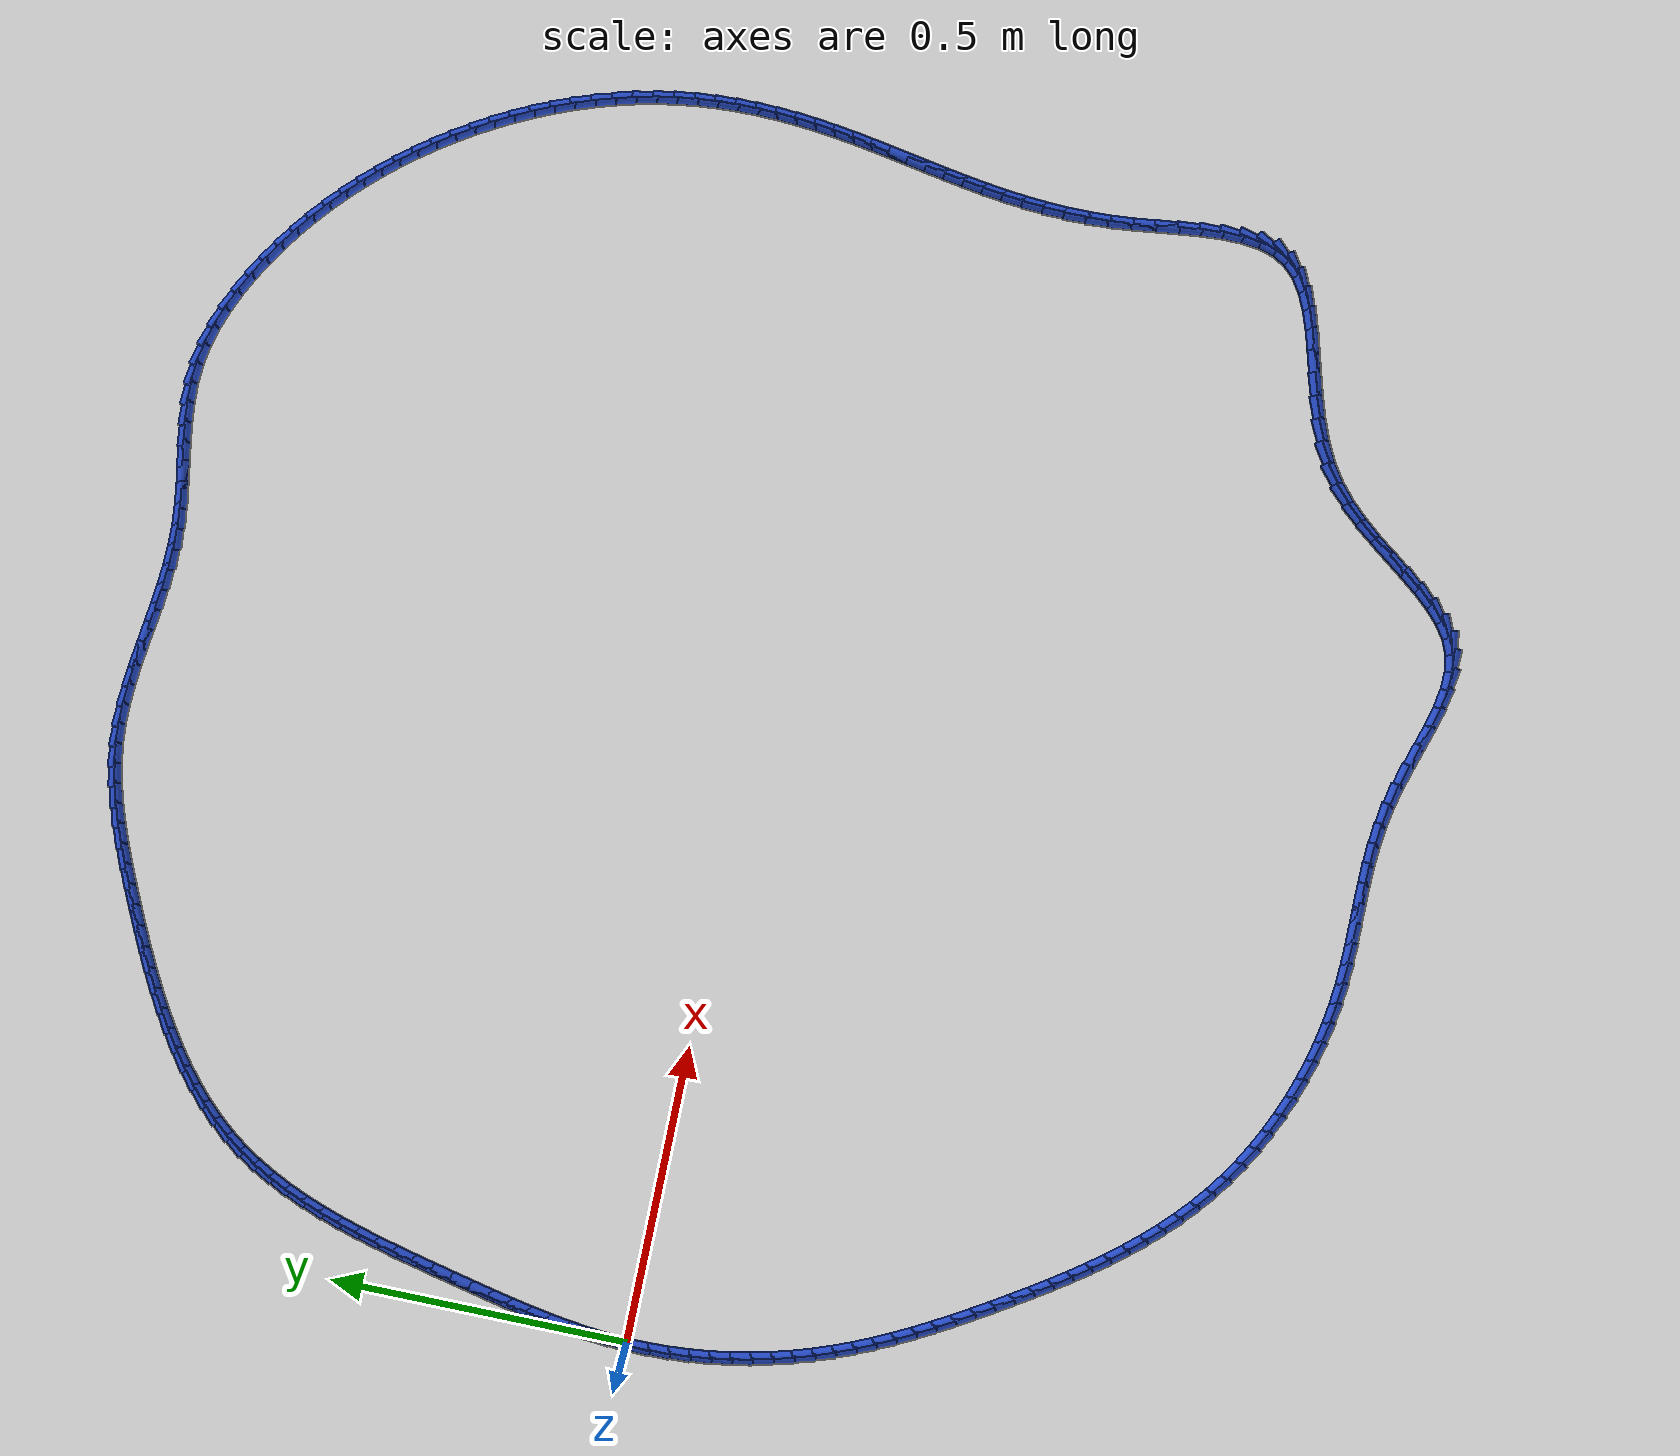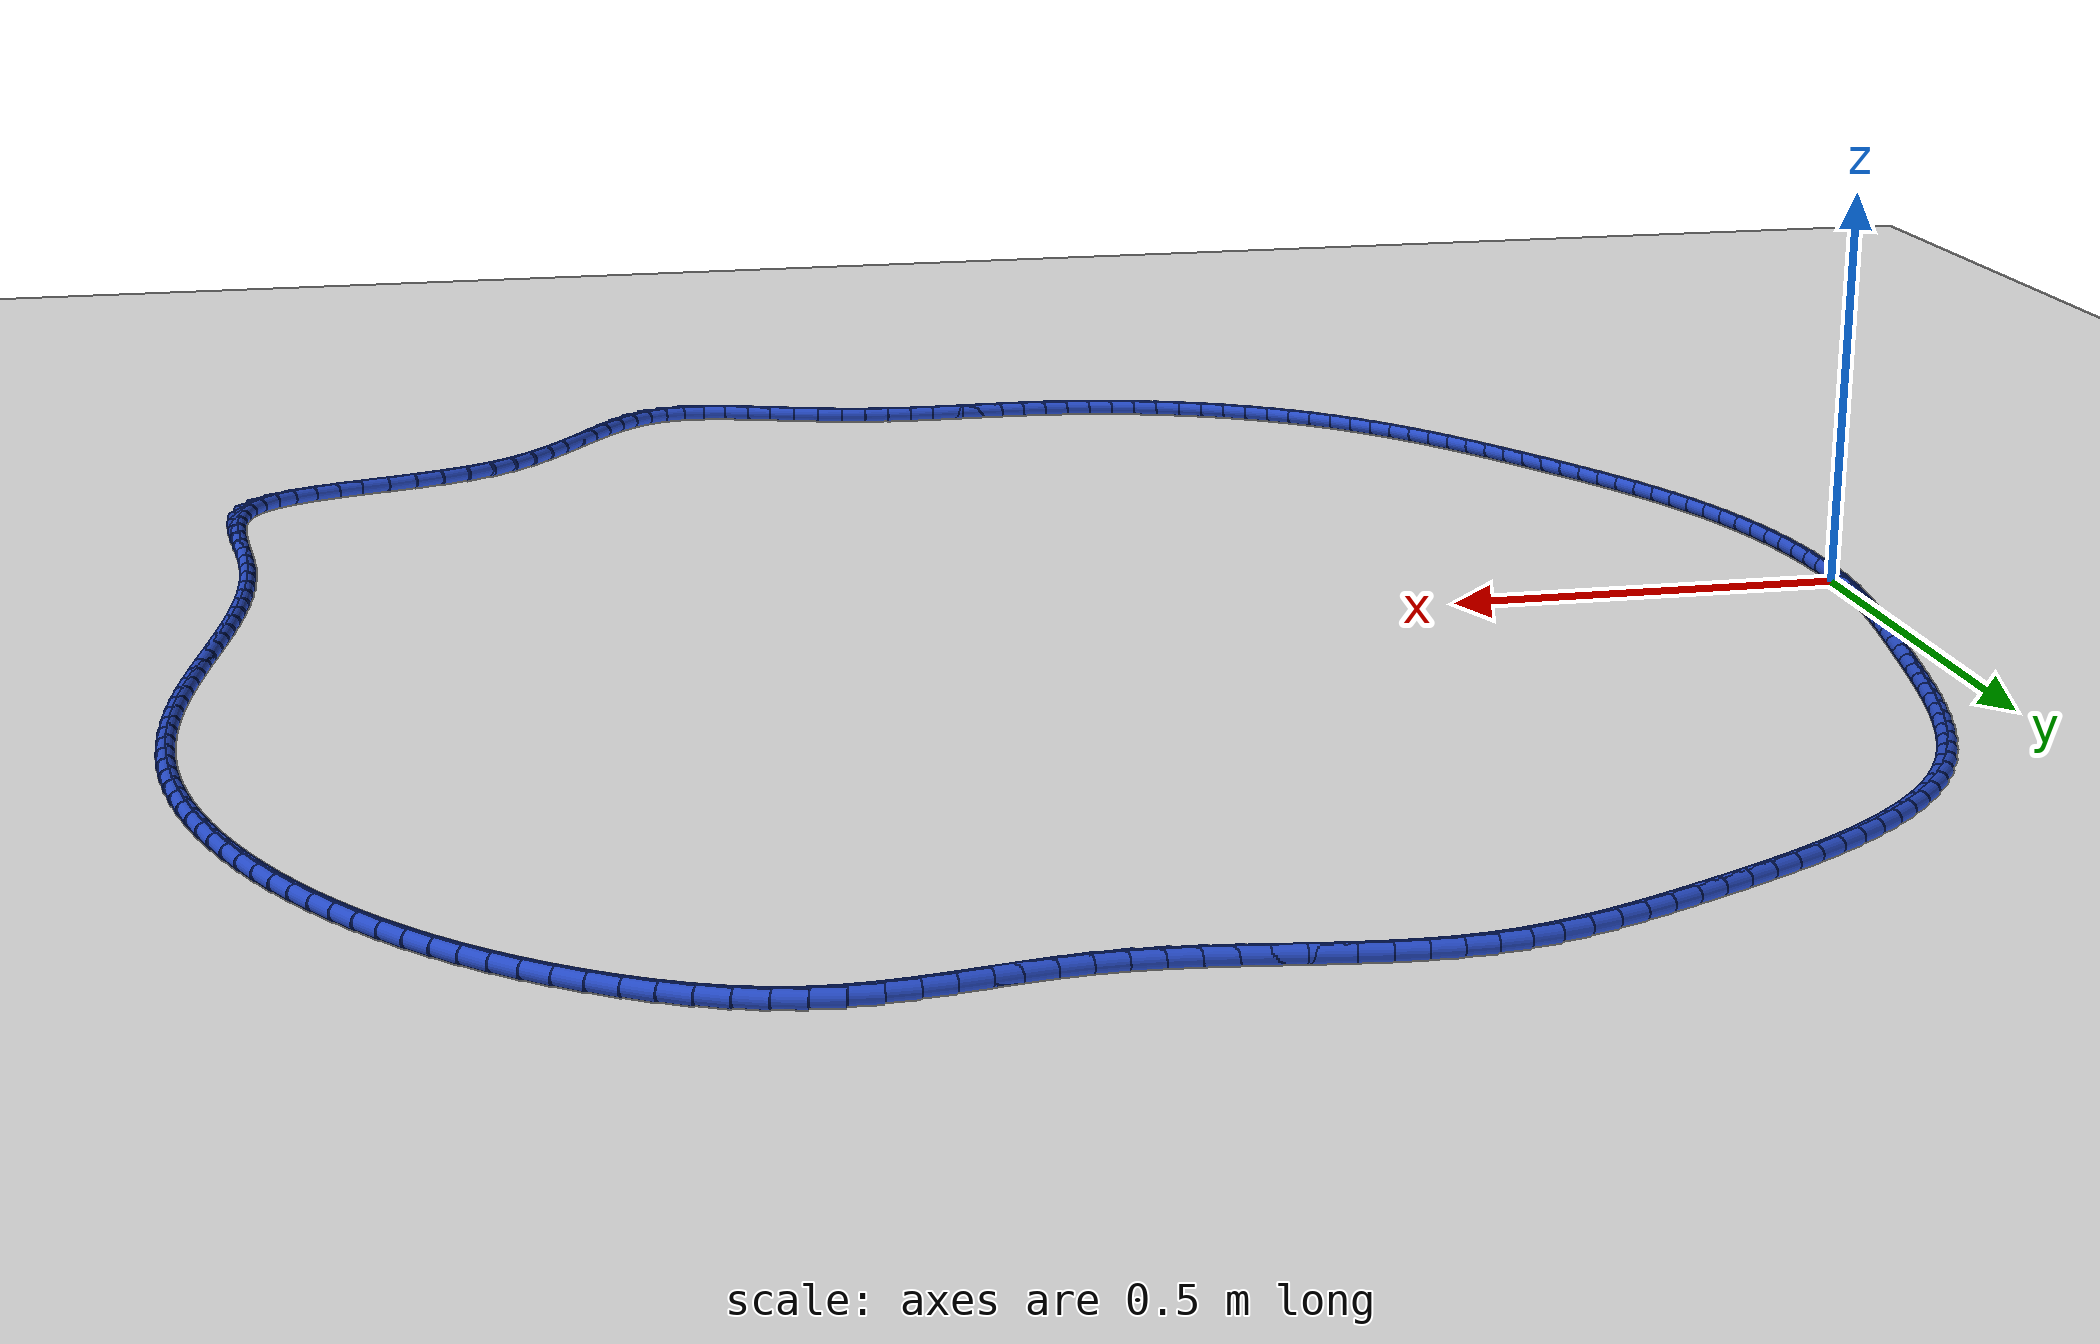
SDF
<sdf version="1.6">
 <world name="default">
  <light name="sun" type="directional">
   <pose>0 0 10 0 -0 0</pose>
   <diffuse>0.8 0.8 0.8 1</diffuse>
   <specular>0.2 0.2 0.2 1</specular>
   <attenuation>
    <range>1000</range>
    <constant>0.9</constant>
    <linear>0.01</linear>
    <quadratic>0.001</quadratic>
   </attenuation>
   <direction>-0.5 0.1 -0.9</direction>
  </light>
  <model name="ground_plane">
   <static>1</static>
   <link name="link">
    <collision name="collision">
     <geometry><plane><normal>0 0 1</normal><size>100 100</size></plane></geometry>
     <surface><friction><ode><mu>100</mu><mu2>50</mu2></ode></friction></surface>
    </collision>
    <visual name="visual">
     <cast_shadows>0</cast_shadows>
     <geometry><plane><normal>0 0 1</normal><size>100 100</size></plane></geometry>
     <material>
      <script><uri>file://media/materials/scripts/gazebo.material</uri><name>Gazebo/WhiteGlow</name></script>
     </material>
    </visual>
   </link>
  </model>
  <gravity>0 0 -9.8</gravity>
  <magnetic_field>6e-06 2.3e-05 -4.2e-05</magnetic_field>
  <atmosphere type="adiabatic"/>
  <physics name="default_physics" default="0" type="ode">
   <max_step_size>0.001</max_step_size>
   <real_time_factor>1</real_time_factor>
   <real_time_update_rate>1000</real_time_update_rate>
  </physics>
  <scene><ambient>0.4 0.4 0.4 1</ambient><background>0.7 0.7 0.7 1</background><shadows>1</shadows></scene>
  <spherical_coordinates>
   <surface_model>EARTH_WGS84</surface_model>
   <latitude_deg>0</latitude_deg>
   <longitude_deg>0</longitude_deg>
   <elevation>0</elevation>
   <heading_deg>0</heading_deg>
  </spherical_coordinates>
  <model name="line">
   <link name="link_0">
    <pose>1.3877787807814457e-17 -4.163336342344337e-17 0.01 0 1.57 1.5237938929489383</pose>
    <collision name="collision">
     <geometry><cylinder><radius>0.01</radius><length>0.08</length></cylinder></geometry>
    </collision>
    <visual name="visual">
     <material>
      <script><name>Gazebo/Blue</name><uri>file://media/materials/scripts/gazebo.material</uri></script>
     </material>
     <geometry><cylinder><radius>0.01</radius><length>0.08</length></cylinder></geometry>
    </visual>
   </link>
   <link name="link_1">
    <pose>0.0015833553322793805 0.03366185605702555 0.01 0 1.57 1.4860514094822226</pose>
    <collision name="collision">
     <geometry><cylinder><radius>0.01</radius><length>0.08</length></cylinder></geometry>
    </collision>
    <visual name="visual">
     <material>
      <script><name>Gazebo/Blue</name><uri>file://media/materials/scripts/gazebo.material</uri></script>
     </material>
     <geometry><cylinder><radius>0.01</radius><length>0.08</length></cylinder></geometry>
    </visual>
   </link>
   <link name="link_2">
    <pose>0.004429879619002589 0.06717072970445973 0.01 0 1.57 1.4527619541786687</pose>
    <collision name="collision">
     <geometry><cylinder><radius>0.01</radius><length>0.08</length></cylinder></geometry>
    </collision>
    <visual name="visual">
     <material>
      <script><name>Gazebo/Blue</name><uri>file://media/materials/scripts/gazebo.material</uri></script>
     </material>
     <geometry><cylinder><radius>0.01</radius><length>0.08</length></cylinder></geometry>
    </visual>
   </link>
   <link name="link_3">
    <pose>0.008391074995483631 0.10057440898370419 0.01 0 1.57 1.4240941859864407</pose>
    <collision name="collision">
     <geometry><cylinder><radius>0.01</radius><length>0.08</length></cylinder></geometry>
    </collision>
    <visual name="visual">
     <material>
      <script><name>Gazebo/Blue</name><uri>file://media/materials/scripts/gazebo.material</uri></script>
     </material>
     <geometry><cylinder><radius>0.01</radius><length>0.08</length></cylinder></geometry>
    </visual>
   </link>
   <link name="link_4">
    <pose>0.013318443597036525 0.1339206819361608 0.01 0 1.57 1.400138462734256</pose>
    <collision name="collision">
     <geometry><cylinder><radius>0.01</radius><length>0.08</length></cylinder></geometry>
    </collision>
    <visual name="visual">
     <material>
      <script><name>Gazebo/Blue</name><uri>file://media/materials/scripts/gazebo.material</uri></script>
     </material>
     <geometry><cylinder><radius>0.01</radius><length>0.08</length></cylinder></geometry>
    </visual>
   </link>
   <link name="link_5">
    <pose>0.019063487558975245 0.16725733660323117 0.01 0 1.57 1.3809240227589556</pose>
    <collision name="collision">
     <geometry><cylinder><radius>0.01</radius><length>0.08</length></cylinder></geometry>
    </collision>
    <visual name="visual">
     <material>
      <script><name>Gazebo/Blue</name><uri>file://media/materials/scripts/gazebo.material</uri></script>
     </material>
     <geometry><cylinder><radius>0.01</radius><length>0.08</length></cylinder></geometry>
    </visual>
   </link>
   <link name="link_6">
    <pose>0.025477709016613812 0.2006321610263172 0.01 0 1.57 1.3664350193207166</pose>
    <collision name="collision">
     <geometry><cylinder><radius>0.01</radius><length>0.08</length></cylinder></geometry>
    </collision>
    <visual name="visual">
     <material>
      <script><name>Gazebo/Blue</name><uri>file://media/materials/scripts/gazebo.material</uri></script>
     </material>
     <geometry><cylinder><radius>0.01</radius><length>0.08</length></cylinder></geometry>
    </visual>
   </link>
   <link name="link_7">
    <pose>0.03241261010526623 0.23409294324682067 0.01 0 1.57 1.356624095651733</pose>
    <collision name="collision">
     <geometry><cylinder><radius>0.01</radius><length>0.08</length></cylinder></geometry>
    </collision>
    <visual name="visual">
     <material>
      <script><name>Gazebo/Blue</name><uri>file://media/materials/scripts/gazebo.material</uri></script>
     </material>
     <geometry><cylinder><radius>0.01</radius><length>0.08</length></cylinder></geometry>
    </visual>
   </link>
   <link name="link_8">
    <pose>0.03971969296024647 0.26768747130614323 0.01 0 1.57 1.3514228529556096</pose>
    <collision name="collision">
     <geometry><cylinder><radius>0.01</radius><length>0.08</length></cylinder></geometry>
    </collision>
    <visual name="visual">
     <material>
      <script><name>Gazebo/Blue</name><uri>file://media/materials/scripts/gazebo.material</uri></script>
     </material>
     <geometry><cylinder><radius>0.01</radius><length>0.08</length></cylinder></geometry>
    </visual>
   </link>
   <link name="link_9">
    <pose>0.04725045971686853 0.3014635332456866 0.01 0 1.57 1.3500065095173566</pose>
    <collision name="collision">
     <geometry><cylinder><radius>0.01</radius><length>0.08</length></cylinder></geometry>
    </collision>
    <visual name="visual">
     <material>
      <script><name>Gazebo/Blue</name><uri>file://media/materials/scripts/gazebo.material</uri></script>
     </material>
     <geometry><cylinder><radius>0.01</radius><length>0.08</length></cylinder></geometry>
    </visual>
   </link>
   <link name="link_10">
    <pose>0.05487967655711953 0.33545442156473815 0.01 0 1.57 1.3464245933959476</pose>
    <collision name="collision">
     <geometry><cylinder><radius>0.01</radius><length>0.08</length></cylinder></geometry>
    </collision>
    <visual name="visual">
     <material>
      <script><name>Gazebo/Blue</name><uri>file://media/materials/scripts/gazebo.material</uri></script>
     </material>
     <geometry><cylinder><radius>0.01</radius><length>0.08</length></cylinder></geometry>
    </visual>
   </link>
   <link name="link_11">
    <pose>0.0626671893206778 0.3695781078981471 0.01 0 1.57 1.3378747662530512</pose>
    <collision name="collision">
     <geometry><cylinder><radius>0.01</radius><length>0.08</length></cylinder></geometry>
    </collision>
    <visual name="visual">
     <material>
      <script><name>Gazebo/Blue</name><uri>file://media/materials/scripts/gazebo.material</uri></script>
     </material>
     <geometry><cylinder><radius>0.01</radius><length>0.08</length></cylinder></geometry>
    </visual>
   </link>
   <link name="link_12">
    <pose>0.07076123481008033 0.4036974885560495 0.01 0 1.57 1.3242959916823867</pose>
    <collision name="collision">
     <geometry><cylinder><radius>0.01</radius><length>0.08</length></cylinder></geometry>
    </collision>
    <visual name="visual">
     <material>
      <script><name>Gazebo/Blue</name><uri>file://media/materials/scripts/gazebo.material</uri></script>
     </material>
     <geometry><cylinder><radius>0.01</radius><length>0.08</length></cylinder></geometry>
    </visual>
   </link>
   <link name="link_13">
    <pose>0.07931059750249457 0.4376751185992369 0.01 0 1.57 1.305567013321524</pose>
    <collision name="collision">
     <geometry><cylinder><radius>0.01</radius><length>0.08</length></cylinder></geometry>
    </collision>
    <visual name="visual">
     <material>
      <script><name>Gazebo/Blue</name><uri>file://media/materials/scripts/gazebo.material</uri></script>
     </material>
     <geometry><cylinder><radius>0.01</radius><length>0.08</length></cylinder></geometry>
    </visual>
   </link>
   <link name="link_14">
    <pose>0.08846406187508797 0.4713735530885005 0.01 0 1.57 1.2814962101043426</pose>
    <collision name="collision">
     <geometry><cylinder><radius>0.01</radius><length>0.08</length></cylinder></geometry>
    </collision>
    <visual name="visual">
     <material>
      <script><name>Gazebo/Blue</name><uri>file://media/materials/scripts/gazebo.material</uri></script>
     </material>
     <geometry><cylinder><radius>0.01</radius><length>0.08</length></cylinder></geometry>
    </visual>
   </link>
   <link name="link_15">
    <pose>0.09837041240502796 0.5046553470846321 0.01 0 1.57 1.2518317260614966</pose>
    <collision name="collision">
     <geometry><cylinder><radius>0.01</radius><length>0.08</length></cylinder></geometry>
    </collision>
    <visual name="visual">
     <material>
      <script><name>Gazebo/Blue</name><uri>file://media/materials/scripts/gazebo.material</uri></script>
     </material>
     <geometry><cylinder><radius>0.01</radius><length>0.08</length></cylinder></geometry>
    </visual>
   </link>
   <link name="link_16">
    <pose>0.1091784335694821 0.5373830556484231 0.01 0 1.57 1.2162766544617851</pose>
    <collision name="collision">
     <geometry><cylinder><radius>0.01</radius><length>0.08</length></cylinder></geometry>
    </collision>
    <visual name="visual">
     <material>
      <script><name>Gazebo/Blue</name><uri>file://media/materials/scripts/gazebo.material</uri></script>
     </material>
     <geometry><cylinder><radius>0.01</radius><length>0.08</length></cylinder></geometry>
    </visual>
   </link>
   <link name="link_17">
    <pose>0.12103690984561777 0.5694192338406652 0.01 0 1.57 1.1745122266760488</pose>
    <collision name="collision">
     <geometry><cylinder><radius>0.01</radius><length>0.08</length></cylinder></geometry>
    </collision>
    <visual name="visual">
     <material>
      <script><name>Gazebo/Blue</name><uri>file://media/materials/scripts/gazebo.material</uri></script>
     </material>
     <geometry><cylinder><radius>0.01</radius><length>0.08</length></cylinder></geometry>
    </visual>
   </link>
   <link name="link_18">
    <pose>0.13409462571060243 0.6006264367221495 0.01 0 1.57 1.1262324496705332</pose>
    <collision name="collision">
     <geometry><cylinder><radius>0.01</radius><length>0.08</length></cylinder></geometry>
    </collision>
    <visual name="visual">
     <material>
      <script><name>Gazebo/Blue</name><uri>file://media/materials/scripts/gazebo.material</uri></script>
     </material>
     <geometry><cylinder><radius>0.01</radius><length>0.08</length></cylinder></geometry>
    </visual>
   </link>
   <link name="link_19">
    <pose>0.14850036564160363 0.630867219353668 0.01 0 1.57 1.0711934784425845</pose>
    <collision name="collision">
     <geometry><cylinder><radius>0.01</radius><length>0.08</length></cylinder></geometry>
    </collision>
    <visual name="visual">
     <material>
      <script><name>Gazebo/Blue</name><uri>file://media/materials/scripts/gazebo.material</uri></script>
     </material>
     <geometry><cylinder><radius>0.01</radius><length>0.08</length></cylinder></geometry>
    </visual>
   </link>
   <link name="link_20">
    <pose>0.16440291411578872 0.6600041367960119 0.01 0 1.57 1.0092794283910438</pose>
    <collision name="collision">
     <geometry><cylinder><radius>0.01</radius><length>0.08</length></cylinder></geometry>
    </collision>
    <visual name="visual">
     <material>
      <script><name>Gazebo/Blue</name><uri>file://media/materials/scripts/gazebo.material</uri></script>
     </material>
     <geometry><cylinder><radius>0.01</radius><length>0.08</length></cylinder></geometry>
    </visual>
   </link>
   <link name="link_21">
    <pose>0.1819510556103252 0.6878997441099728 0.01 0 1.57 0.9405877349512616</pose>
    <collision name="collision">
     <geometry><cylinder><radius>0.01</radius><length>0.08</length></cylinder></geometry>
    </collision>
    <visual name="visual">
     <material>
      <script><name>Gazebo/Blue</name><uri>file://media/materials/scripts/gazebo.material</uri></script>
     </material>
     <geometry><cylinder><radius>0.01</radius><length>0.08</length></cylinder></geometry>
    </visual>
   </link>
   <link name="link_22">
    <pose>0.20129343419691842 0.7144167034551361 0.01 0 1.57 0.8683387658101243</pose>
    <collision name="collision">
     <geometry><cylinder><radius>0.01</radius><length>0.08</length></cylinder></geometry>
    </collision>
    <visual name="visual">
     <material>
      <script><name>Gazebo/Blue</name><uri>file://media/materials/scripts/gazebo.material</uri></script>
     </material>
     <geometry><cylinder><radius>0.01</radius><length>0.08</length></cylinder></geometry>
    </visual>
   </link>
   <link name="link_23">
    <pose>0.22250457253174716 0.7394742154910007 0.01 0 1.57 0.8005762010262795</pose>
    <collision name="collision">
     <geometry><cylinder><radius>0.01</radius><length>0.08</length></cylinder></geometry>
    </collision>
    <visual name="visual">
     <material>
      <script><name>Gazebo/Blue</name><uri>file://media/materials/scripts/gazebo.material</uri></script>
     </material>
     <geometry><cylinder><radius>0.01</radius><length>0.08</length></cylinder></geometry>
    </visual>
   </link>
   <link name="link_24">
    <pose>0.24546334240747048 0.7631407198824405 0.01 0 1.57 0.7388628193276238</pose>
    <collision name="collision">
     <geometry><cylinder><radius>0.01</radius><length>0.08</length></cylinder></geometry>
    </collision>
    <visual name="visual">
     <material>
      <script><name>Gazebo/Blue</name><uri>file://media/materials/scripts/gazebo.material</uri></script>
     </material>
     <geometry><cylinder><radius>0.01</radius><length>0.08</length></cylinder></geometry>
    </visual>
   </link>
   <link name="link_25">
    <pose>0.27001670891289004 0.7855089941616046 0.01 0 1.57 0.683287677241117</pose>
    <collision name="collision">
     <geometry><cylinder><radius>0.01</radius><length>0.08</length></cylinder></geometry>
    </collision>
    <visual name="visual">
     <material>
      <script><name>Gazebo/Blue</name><uri>file://media/materials/scripts/gazebo.material</uri></script>
     </material>
     <geometry><cylinder><radius>0.01</radius><length>0.08</length></cylinder></geometry>
    </visual>
   </link>
   <link name="link_26">
    <pose>0.296011637136807 0.8066718158606411 0.01 0 1.57 0.6337558066527689</pose>
    <collision name="collision">
     <geometry><cylinder><radius>0.01</radius><length>0.08</length></cylinder></geometry>
    </collision>
    <visual name="visual">
     <material>
      <script><name>Gazebo/Blue</name><uri>file://media/materials/scripts/gazebo.material</uri></script>
     </material>
     <geometry><cylinder><radius>0.01</radius><length>0.08</length></cylinder></geometry>
    </visual>
   </link>
   <link name="link_27">
    <pose>0.32329509216802294 0.8267219625116993 0.01 0 1.57 0.5900530305081407</pose>
    <collision name="collision">
     <geometry><cylinder><radius>0.01</radius><length>0.08</length></cylinder></geometry>
    </collision>
    <visual name="visual">
     <material>
      <script><name>Gazebo/Blue</name><uri>file://media/materials/scripts/gazebo.material</uri></script>
     </material>
     <geometry><cylinder><radius>0.01</radius><length>0.08</length></cylinder></geometry>
    </visual>
   </link>
   <link name="link_28">
    <pose>0.351714039095339 0.8457522116469275 0.01 0 1.57 0.551900593607712</pose>
    <collision name="collision">
     <geometry><cylinder><radius>0.01</radius><length>0.08</length></cylinder></geometry>
    </collision>
    <visual name="visual">
     <material>
      <script><name>Gazebo/Blue</name><uri>file://media/materials/scripts/gazebo.material</uri></script>
     </material>
     <geometry><cylinder><radius>0.01</radius><length>0.08</length></cylinder></geometry>
    </visual>
   </link>
   <link name="link_29">
    <pose>0.38111544300755673 0.8638553407984746 0.01 0 1.57 0.518997206537013</pose>
    <collision name="collision">
     <geometry><cylinder><radius>0.01</radius><length>0.08</length></cylinder></geometry>
    </collision>
    <visual name="visual">
     <material>
      <script><name>Gazebo/Blue</name><uri>file://media/materials/scripts/gazebo.material</uri></script>
     </material>
     <geometry><cylinder><radius>0.01</radius><length>0.08</length></cylinder></geometry>
    </visual>
   </link>
   <link name="link_30">
    <pose>0.4113462689934775 0.881124127498489 0.01 0 1.57 0.4910492915164218</pose>
    <collision name="collision">
     <geometry><cylinder><radius>0.01</radius><length>0.08</length></cylinder></geometry>
    </collision>
    <visual name="visual">
     <material>
      <script><name>Gazebo/Blue</name><uri>file://media/materials/scripts/gazebo.material</uri></script>
     </material>
     <geometry><cylinder><radius>0.01</radius><length>0.08</length></cylinder></geometry>
    </visual>
   </link>
   <link name="link_31">
    <pose>0.44225348214190274 0.8976513492791195 0.01 0 1.57 0.46779166946601</pose>
    <collision name="collision">
     <geometry><cylinder><radius>0.01</radius><length>0.08</length></cylinder></geometry>
    </collision>
    <visual name="visual">
     <material>
      <script><name>Gazebo/Blue</name><uri>file://media/materials/scripts/gazebo.material</uri></script>
     </material>
     <geometry><cylinder><radius>0.01</radius><length>0.08</length></cylinder></geometry>
    </visual>
   </link>
   <link name="link_32">
    <pose>0.4736840475416339 0.9135297836725152 0.01 0 1.57 0.44900126293869186</pose>
    <collision name="collision">
     <geometry><cylinder><radius>0.01</radius><length>0.08</length></cylinder></geometry>
    </collision>
    <visual name="visual">
     <material>
      <script><name>Gazebo/Blue</name><uri>file://media/materials/scripts/gazebo.material</uri></script>
     </material>
     <geometry><cylinder><radius>0.01</radius><length>0.08</length></cylinder></geometry>
    </visual>
   </link>
   <link name="link_33">
    <pose>0.5054849302814723 0.9288522082108248 0.01 0 1.57 0.4345061619689134</pose>
    <collision name="collision">
     <geometry><cylinder><radius>0.01</radius><length>0.08</length></cylinder></geometry>
    </collision>
    <visual name="visual">
     <material>
      <script><name>Gazebo/Blue</name><uri>file://media/materials/scripts/gazebo.material</uri></script>
     </material>
     <geometry><cylinder><radius>0.01</radius><length>0.08</length></cylinder></geometry>
    </visual>
   </link>
   <link name="link_34">
    <pose>0.5375030954502192 0.9437114004261964 0.01 0 1.57 0.42409030544996706</pose>
    <collision name="collision">
     <geometry><cylinder><radius>0.01</radius><length>0.08</length></cylinder></geometry>
    </collision>
    <visual name="visual">
     <material>
      <script><name>Gazebo/Blue</name><uri>file://media/materials/scripts/gazebo.material</uri></script>
     </material>
     <geometry><cylinder><radius>0.01</radius><length>0.08</length></cylinder></geometry>
    </visual>
   </link>
   <link name="link_35">
    <pose>0.5695870242857025 0.9581968956375084 0.01 0 1.57 0.412637379855925</pose>
    <collision name="collision">
     <geometry><cylinder><radius>0.01</radius><length>0.08</length></cylinder></geometry>
    </collision>
    <visual name="visual">
     <material>
      <script><name>Gazebo/Blue</name><uri>file://media/materials/scripts/gazebo.material</uri></script>
     </material>
     <geometry><cylinder><radius>0.01</radius><length>0.08</length></cylinder></geometry>
    </visual>
   </link>
   <link name="link_36">
    <pose>0.6016603002611548 0.9722376265711373 0.01 0 1.57 0.3926946823154604</pose>
    <collision name="collision">
     <geometry><cylinder><radius>0.01</radius><length>0.08</length></cylinder></geometry>
    </collision>
    <visual name="visual">
     <material>
      <script><name>Gazebo/Blue</name><uri>file://media/materials/scripts/gazebo.material</uri></script>
     </material>
     <geometry><cylinder><radius>0.01</radius><length>0.08</length></cylinder></geometry>
    </visual>
   </link>
   <link name="link_37">
    <pose>0.6337546072340434 0.9855313583741586 0.01 0 1.57 0.36335069937466385</pose>
    <collision name="collision">
     <geometry><cylinder><radius>0.01</radius><length>0.08</length></cylinder></geometry>
    </collision>
    <visual name="visual">
     <material>
      <script><name>Gazebo/Blue</name><uri>file://media/materials/scripts/gazebo.material</uri></script>
     </material>
     <geometry><cylinder><radius>0.01</radius><length>0.08</length></cylinder></geometry>
    </visual>
   </link>
   <link name="link_38">
    <pose>0.665910020502345 0.9977579114934229 0.01 0 1.57 0.3241759028659427</pose>
    <collision name="collision">
     <geometry><cylinder><radius>0.01</radius><length>0.08</length></cylinder></geometry>
    </collision>
    <visual name="visual">
     <material>
      <script><name>Gazebo/Blue</name><uri>file://media/materials/scripts/gazebo.material</uri></script>
     </material>
     <geometry><cylinder><radius>0.01</radius><length>0.08</length></cylinder></geometry>
    </visual>
   </link>
   <link name="link_39">
    <pose>0.6981666153640363 1.0085971063757786 0.01 0 1.57 0.27473260615598905</pose>
    <collision name="collision">
     <geometry><cylinder><radius>0.01</radius><length>0.08</length></cylinder></geometry>
    </collision>
    <visual name="visual">
     <material>
      <script><name>Gazebo/Blue</name><uri>file://media/materials/scripts/gazebo.material</uri></script>
     </material>
     <geometry><cylinder><radius>0.01</radius><length>0.08</length></cylinder></geometry>
    </visual>
   </link>
   <link name="link_40">
    <pose>0.7305644671170941 1.0177287634680758 0.01 0 1.57 0.2146909953033992</pose>
    <collision name="collision">
     <geometry><cylinder><radius>0.01</radius><length>0.08</length></cylinder></geometry>
    </collision>
    <visual name="visual">
     <material>
      <script><name>Gazebo/Blue</name><uri>file://media/materials/scripts/gazebo.material</uri></script>
     </material>
     <geometry><cylinder><radius>0.01</radius><length>0.08</length></cylinder></geometry>
    </visual>
   </link>
   <link name="link_41">
    <pose>0.7631436510594952 1.0248327032171642 0.01 0 1.57 0.14399514060104668</pose>
    <collision name="collision">
     <geometry><cylinder><radius>0.01</radius><length>0.08</length></cylinder></geometry>
    </collision>
    <visual name="visual">
     <material>
      <script><name>Gazebo/Blue</name><uri>file://media/materials/scripts/gazebo.material</uri></script>
     </material>
     <geometry><cylinder><radius>0.01</radius><length>0.08</length></cylinder></geometry>
    </visual>
   </link>
   <link name="link_42">
    <pose>0.7959442424892157 1.0295887460698931 0.01 0 1.57 0.06546857079153841</pose>
    <collision name="collision">
     <geometry><cylinder><radius>0.01</radius><length>0.08</length></cylinder></geometry>
    </collision>
    <visual name="visual">
     <material>
      <script><name>Gazebo/Blue</name><uri>file://media/materials/scripts/gazebo.material</uri></script>
     </material>
     <geometry><cylinder><radius>0.01</radius><length>0.08</length></cylinder></geometry>
    </visual>
   </link>
   <link name="link_43">
    <pose>0.8289994796551866 1.0317559223585735 0.01 0 1.57 -0.004415462437230972</pose>
    <collision name="collision">
     <geometry><cylinder><radius>0.01</radius><length>0.08</length></cylinder></geometry>
    </collision>
    <visual name="visual">
     <material>
      <script><name>Gazebo/Blue</name><uri>file://media/materials/scripts/gazebo.material</uri></script>
     </material>
     <geometry><cylinder><radius>0.01</radius><length>0.08</length></cylinder></geometry>
    </visual>
   </link>
   <link name="link_44">
    <pose>0.8622980938739451 1.0316088926227651 0.01 0 1.57 -0.05901914920225609</pose>
    <collision name="collision">
     <geometry><cylinder><radius>0.01</radius><length>0.08</length></cylinder></geometry>
    </collision>
    <visual name="visual">
     <material>
      <script><name>Gazebo/Blue</name><uri>file://media/materials/scripts/gazebo.material</uri></script>
     </material>
     <geometry><cylinder><radius>0.01</radius><length>0.08</length></cylinder></geometry>
    </visual>
   </link>
   <link name="link_45">
    <pose>0.8958110033300841 1.0296286894978557 0.01 0 1.57 -0.09855171799333817</pose>
    <collision name="collision">
     <geometry><cylinder><radius>0.01</radius><length>0.08</length></cylinder></geometry>
    </collision>
    <visual name="visual">
     <material>
      <script><name>Gazebo/Blue</name><uri>file://media/materials/scripts/gazebo.material</uri></script>
     </material>
     <geometry><cylinder><radius>0.01</radius><length>0.08</length></cylinder></geometry>
    </visual>
   </link>
   <link name="link_46">
    <pose>0.9295090789925875 1.0262968926305158 0.01 0 1.57 -0.12348374062670416</pose>
    <collision name="collision">
     <geometry><cylinder><radius>0.01</radius><length>0.08</length></cylinder></geometry>
    </collision>
    <visual name="visual">
     <material>
      <script><name>Gazebo/Blue</name><uri>file://media/materials/scripts/gazebo.material</uri></script>
     </material>
     <geometry><cylinder><radius>0.01</radius><length>0.08</length></cylinder></geometry>
    </visual>
   </link>
   <link name="link_47">
    <pose>0.9633631918304394 1.0220950816674175 0.01 0 1.57 -0.13426987021979914</pose>
    <collision name="collision">
     <geometry><cylinder><radius>0.01</radius><length>0.08</length></cylinder></geometry>
    </collision>
    <visual name="visual">
     <material>
      <script><name>Gazebo/Blue</name><uri>file://media/materials/scripts/gazebo.material</uri></script>
     </material>
     <geometry><cylinder><radius>0.01</radius><length>0.08</length></cylinder></geometry>
    </visual>
   </link>
   <link name="link_48">
    <pose>0.997344212812623 1.017504836255232 0.01 0 1.57 -0.13120372640908792</pose>
    <collision name="collision">
     <geometry><cylinder><radius>0.01</radius><length>0.08</length></cylinder></geometry>
    </collision>
    <visual name="visual">
     <material>
      <script><name>Gazebo/Blue</name><uri>file://media/materials/scripts/gazebo.material</uri></script>
     </material>
     <geometry><cylinder><radius>0.01</radius><length>0.08</length></cylinder></geometry>
    </visual>
   </link>
   <link name="link_49">
    <pose>1.031423012908123 1.0130077360406309 0.01 0 1.57 -0.11436461070944176</pose>
    <collision name="collision">
     <geometry><cylinder><radius>0.01</radius><length>0.08</length></cylinder></geometry>
    </collision>
    <visual name="visual">
     <material>
      <script><name>Gazebo/Blue</name><uri>file://media/materials/scripts/gazebo.material</uri></script>
     </material>
     <geometry><cylinder><radius>0.01</radius><length>0.08</length></cylinder></geometry>
    </visual>
   </link>
   <link name="link_50">
    <pose>1.0655704630859228 1.009085360670285 0.01 0 1.57 -0.08363959659428066</pose>
    <collision name="collision">
     <geometry><cylinder><radius>0.01</radius><length>0.08</length></cylinder></geometry>
    </collision>
    <visual name="visual">
     <material>
      <script><name>Gazebo/Blue</name><uri>file://media/materials/scripts/gazebo.material</uri></script>
     </material>
     <geometry><cylinder><radius>0.01</radius><length>0.08</length></cylinder></geometry>
    </visual>
   </link>
   <link name="link_51">
    <pose>1.0997574343150065 1.0062192897908666 0.01 0 1.57 -0.0388193527741868</pose>
    <collision name="collision">
     <geometry><cylinder><radius>0.01</radius><length>0.08</length></cylinder></geometry>
    </collision>
    <visual name="visual">
     <material>
      <script><name>Gazebo/Blue</name><uri>file://media/materials/scripts/gazebo.material</uri></script>
     </material>
     <geometry><cylinder><radius>0.01</radius><length>0.08</length></cylinder></geometry>
    </visual>
   </link>
   <link name="link_52">
    <pose>1.1339547975643576 1.0048911030490466 0.01 0 1.57 0.020213358716206664</pose>
    <collision name="collision">
     <geometry><cylinder><radius>0.01</radius><length>0.08</length></cylinder></geometry>
    </collision>
    <visual name="visual">
     <material>
      <script><name>Gazebo/Blue</name><uri>file://media/materials/scripts/gazebo.material</uri></script>
     </material>
     <geometry><cylinder><radius>0.01</radius><length>0.08</length></cylinder></geometry>
    </visual>
   </link>
   <link name="link_53">
    <pose>1.1681334258048288 1.0055820620286393 0.01 0 1.57 0.08481698721427056</pose>
    <collision name="collision">
     <geometry><cylinder><radius>0.01</radius><length>0.08</length></cylinder></geometry>
    </collision>
    <visual name="visual">
     <material>
      <script><name>Gazebo/Blue</name><uri>file://media/materials/scripts/gazebo.material</uri></script>
     </material>
     <geometry><cylinder><radius>0.01</radius><length>0.08</length></cylinder></geometry>
    </visual>
   </link>
   <link name="link_54">
    <pose>1.202266013352895 1.0084840474950658 0.01 0 1.57 0.13081095137444468</pose>
    <collision name="collision">
     <geometry><cylinder><radius>0.01</radius><length>0.08</length></cylinder></geometry>
    </collision>
    <visual name="visual">
     <material>
      <script><name>Gazebo/Blue</name><uri>file://media/materials/scripts/gazebo.material</uri></script>
     </material>
     <geometry><cylinder><radius>0.01</radius><length>0.08</length></cylinder></geometry>
    </visual>
   </link>
   <link name="link_55">
    <pose>1.2363304363367107 1.0129656385376251 0.01 0 1.57 0.15429955857101207</pose>
    <collision name="collision">
     <geometry><cylinder><radius>0.01</radius><length>0.08</length></cylinder></geometry>
    </collision>
    <visual name="visual">
     <material>
      <script><name>Gazebo/Blue</name><uri>file://media/materials/scripts/gazebo.material</uri></script>
     </material>
     <geometry><cylinder><radius>0.01</radius><length>0.08</length></cylinder></geometry>
    </visual>
   </link>
   <link name="link_56">
    <pose>1.2703054862540362 1.018249977595118 0.01 0 1.57 0.15554168414504255</pose>
    <collision name="collision">
     <geometry><cylinder><radius>0.01</radius><length>0.08</length></cylinder></geometry>
    </collision>
    <visual name="visual">
     <material>
      <script><name>Gazebo/Blue</name><uri>file://media/materials/scripts/gazebo.material</uri></script>
     </material>
     <geometry><cylinder><radius>0.01</radius><length>0.08</length></cylinder></geometry>
    </visual>
   </link>
   <link name="link_57">
    <pose>1.3041699546026353 1.0235602071063477 0.01 0 1.57 0.1343445101931664</pose>
    <collision name="collision">
     <geometry><cylinder><radius>0.01</radius><length>0.08</length></cylinder></geometry>
    </collision>
    <visual name="visual">
     <material>
      <script><name>Gazebo/Blue</name><uri>file://media/materials/scripts/gazebo.material</uri></script>
     </material>
     <geometry><cylinder><radius>0.01</radius><length>0.08</length></cylinder></geometry>
    </visual>
   </link>
   <link name="link_58">
    <pose>1.3379026328802706 1.0281194695101155 0.01 0 1.57 0.09003190756228516</pose>
    <collision name="collision">
     <geometry><cylinder><radius>0.01</radius><length>0.08</length></cylinder></geometry>
    </collision>
    <visual name="visual">
     <material>
      <script><name>Gazebo/Blue</name><uri>file://media/materials/scripts/gazebo.material</uri></script>
     </material>
     <geometry><cylinder><radius>0.01</radius><length>0.08</length></cylinder></geometry>
    </visual>
   </link>
   <link name="link_59">
    <pose>1.3714823125847047 1.031150907245224 0.01 0 1.57 0.02175215081615469</pose>
    <collision name="collision">
     <geometry><cylinder><radius>0.01</radius><length>0.08</length></cylinder></geometry>
    </collision>
    <visual name="visual">
     <material>
      <script><name>Gazebo/Blue</name><uri>file://media/materials/scripts/gazebo.material</uri></script>
     </material>
     <geometry><cylinder><radius>0.01</radius><length>0.08</length></cylinder></geometry>
    </visual>
   </link>
   <link name="link_60">
    <pose>1.4048877852137003 1.0318776627504758 0.01 0 1.57 -0.0706780919763702</pose>
    <collision name="collision">
     <geometry><cylinder><radius>0.01</radius><length>0.08</length></cylinder></geometry>
    </collision>
    <visual name="visual">
     <material>
      <script><name>Gazebo/Blue</name><uri>file://media/materials/scripts/gazebo.material</uri></script>
     </material>
     <geometry><cylinder><radius>0.01</radius><length>0.08</length></cylinder></geometry>
    </visual>
   </link>
   <link name="link_61">
    <pose>1.438097530410926 1.0295265451018887 0.01 0 1.57 -0.1748310320683953</pose>
    <collision name="collision">
     <geometry><cylinder><radius>0.01</radius><length>0.08</length></cylinder></geometry>
    </collision>
    <visual name="visual">
     <material>
      <script><name>Gazebo/Blue</name><uri>file://media/materials/scripts/gazebo.material</uri></script>
     </material>
     <geometry><cylinder><radius>0.01</radius><length>0.08</length></cylinder></geometry>
    </visual>
   </link>
   <link name="link_62">
    <pose>1.4710576838354428 1.0237046490926218 0.01 0 1.57 -0.26878809851710617</pose>
    <collision name="collision">
     <geometry><cylinder><radius>0.01</radius><length>0.08</length></cylinder></geometry>
    </collision>
    <visual name="visual">
     <material>
      <script><name>Gazebo/Blue</name><uri>file://media/materials/scripts/gazebo.material</uri></script>
     </material>
     <geometry><cylinder><radius>0.01</radius><length>0.08</length></cylinder></geometry>
    </visual>
   </link>
   <link name="link_63">
    <pose>1.5036542730209062 1.0147257932498852 0.01 0 1.57 -0.35063442356578867</pose>
    <collision name="collision">
     <geometry><cylinder><radius>0.01</radius><length>0.08</length></cylinder></geometry>
    </collision>
    <visual name="visual">
     <material>
      <script><name>Gazebo/Blue</name><uri>file://media/materials/scripts/gazebo.material</uri></script>
     </material>
     <geometry><cylinder><radius>0.01</radius><length>0.08</length></cylinder></geometry>
    </visual>
   </link>
   <link name="link_64">
    <pose>1.5357667830568489 1.0029807191542888 0.01 0 1.57 -0.4213217533757041</pose>
    <collision name="collision">
     <geometry><cylinder><radius>0.01</radius><length>0.08</length></cylinder></geometry>
    </collision>
    <visual name="visual">
     <material>
      <script><name>Gazebo/Blue</name><uri>file://media/materials/scripts/gazebo.material</uri></script>
     </material>
     <geometry><cylinder><radius>0.01</radius><length>0.08</length></cylinder></geometry>
    </visual>
   </link>
   <link name="link_65">
    <pose>1.5672746990328021 0.9888601683864421 0.01 0 1.57 -0.48202777366266325</pose>
    <collision name="collision">
     <geometry><cylinder><radius>0.01</radius><length>0.08</length></cylinder></geometry>
    </collision>
    <visual name="visual">
     <material>
      <script><name>Gazebo/Blue</name><uri>file://media/materials/scripts/gazebo.material</uri></script>
     </material>
     <geometry><cylinder><radius>0.01</radius><length>0.08</length></cylinder></geometry>
    </visual>
   </link>
   <link name="link_66">
    <pose>1.5980575060382998 0.9727548825269556 0.01 0 1.57 -0.5339340986630283</pose>
    <collision name="collision">
     <geometry><cylinder><radius>0.01</radius><length>0.08</length></cylinder></geometry>
    </collision>
    <visual name="visual">
     <material>
      <script><name>Gazebo/Blue</name><uri>file://media/materials/scripts/gazebo.material</uri></script>
     </material>
     <geometry><cylinder><radius>0.01</radius><length>0.08</length></cylinder></geometry>
    </visual>
   </link>
   <link name="link_67">
    <pose>1.6279946891628727 0.955055603156439 0.01 0 1.57 -0.5788261377598799</pose>
    <collision name="collision">
     <geometry><cylinder><radius>0.01</radius><length>0.08</length></cylinder></geometry>
    </collision>
    <visual name="visual">
     <material>
      <script><name>Gazebo/Blue</name><uri>file://media/materials/scripts/gazebo.material</uri></script>
     </material>
     <geometry><cylinder><radius>0.01</radius><length>0.08</length></cylinder></geometry>
    </visual>
   </link>
   <link name="link_68">
    <pose>1.656979142903108 0.9361144945198969 0.01 0 1.57 -0.6215607652828136</pose>
    <collision name="collision">
     <geometry><cylinder><radius>0.01</radius><length>0.08</length></cylinder></geometry>
    </collision>
    <visual name="visual">
     <material>
      <script><name>Gazebo/Blue</name><uri>file://media/materials/scripts/gazebo.material</uri></script>
     </material>
     <geometry><cylinder><radius>0.01</radius><length>0.08</length></cylinder></geometry>
    </visual>
   </link>
   <link name="link_69">
    <pose>1.6849827824959516 0.9160563871996104 0.01 0 1.57 -0.6636873785567908</pose>
    <collision name="collision">
     <geometry><cylinder><radius>0.01</radius><length>0.08</length></cylinder></geometry>
    </collision>
    <visual name="visual">
     <material>
      <script><name>Gazebo/Blue</name><uri>file://media/materials/scripts/gazebo.material</uri></script>
     </material>
     <geometry><cylinder><radius>0.01</radius><length>0.08</length></cylinder></geometry>
    </visual>
   </link>
   <link name="link_70">
    <pose>1.7120063702527462 0.8949231220329945 0.01 0 1.57 -0.7051404682241248</pose>
    <collision name="collision">
     <geometry><cylinder><radius>0.01</radius><length>0.08</length></cylinder></geometry>
    </collision>
    <visual name="visual">
     <material>
      <script><name>Gazebo/Blue</name><uri>file://media/materials/scripts/gazebo.material</uri></script>
     </material>
     <geometry><cylinder><radius>0.01</radius><length>0.08</length></cylinder></geometry>
    </visual>
   </link>
   <link name="link_71">
    <pose>1.7380507108355725 0.8727564180192129 0.01 0 1.57 -0.7458645775239934</pose>
    <collision name="collision">
     <geometry><cylinder><radius>0.01</radius><length>0.08</length></cylinder></geometry>
    </collision>
    <visual name="visual">
     <material>
      <script><name>Gazebo/Blue</name><uri>file://media/materials/scripts/gazebo.material</uri></script>
     </material>
     <geometry><cylinder><radius>0.01</radius><length>0.08</length></cylinder></geometry>
    </visual>
   </link>
   <link name="link_72">
    <pose>1.7631166089065142 0.8495979941574295 0.01 0 1.57 -0.7858165425522354</pose>
    <collision name="collision">
     <geometry><cylinder><radius>0.01</radius><length>0.08</length></cylinder></geometry>
    </collision>
    <visual name="visual">
     <material>
      <script><name>Gazebo/Blue</name><uri>file://media/materials/scripts/gazebo.material</uri></script>
     </material>
     <geometry><cylinder><radius>0.01</radius><length>0.08</length></cylinder></geometry>
    </visual>
   </link>
   <link name="link_73">
    <pose>1.7872048691276536 0.8254895694468083 0.01 0 1.57 -0.8249651487157852</pose>
    <collision name="collision">
     <geometry><cylinder><radius>0.01</radius><length>0.08</length></cylinder></geometry>
    </collision>
    <visual name="visual">
     <material>
      <script><name>Gazebo/Blue</name><uri>file://media/materials/scripts/gazebo.material</uri></script>
     </material>
     <geometry><cylinder><radius>0.01</radius><length>0.08</length></cylinder></geometry>
    </visual>
   </link>
   <link name="link_74">
    <pose>1.8103162961610721 0.8004728628865129 0.01 0 1.57 -0.8632905389196548</pose>
    <collision name="collision">
     <geometry><cylinder><radius>0.01</radius><length>0.08</length></cylinder></geometry>
    </collision>
    <visual name="visual">
     <material>
      <script><name>Gazebo/Blue</name><uri>file://media/materials/scripts/gazebo.material</uri></script>
     </material>
     <geometry><cylinder><radius>0.01</radius><length>0.08</length></cylinder></geometry>
    </visual>
   </link>
   <link name="link_75">
    <pose>1.8324516946688532 0.7745895934757073 0.01 0 1.57 -0.9007834355394135</pose>
    <collision name="collision">
     <geometry><cylinder><radius>0.01</radius><length>0.08</length></cylinder></geometry>
    </collision>
    <visual name="visual">
     <material>
      <script><name>Gazebo/Blue</name><uri>file://media/materials/scripts/gazebo.material</uri></script>
     </material>
     <geometry><cylinder><radius>0.01</radius><length>0.08</length></cylinder></geometry>
    </visual>
   </link>
   <link name="link_76">
    <pose>1.853611869313078 0.7478814802135553 0.01 0 1.57 -0.9374442364813387</pose>
    <collision name="collision">
     <geometry><cylinder><radius>0.01</radius><length>0.08</length></cylinder></geometry>
    </collision>
    <visual name="visual">
     <material>
      <script><name>Gazebo/Blue</name><uri>file://media/materials/scripts/gazebo.material</uri></script>
     </material>
     <geometry><cylinder><radius>0.01</radius><length>0.08</length></cylinder></geometry>
    </visual>
   </link>
   <link name="link_77">
    <pose>1.8737976247558294 0.7203902420992208 0.01 0 1.57 -0.9732820403305039</pose>
    <collision name="collision">
     <geometry><cylinder><radius>0.01</radius><length>0.08</length></cylinder></geometry>
    </collision>
    <visual name="visual">
     <material>
      <script><name>Gazebo/Blue</name><uri>file://media/materials/scripts/gazebo.material</uri></script>
     </material>
     <geometry><cylinder><radius>0.01</radius><length>0.08</length></cylinder></geometry>
    </visual>
   </link>
   <link name="link_78">
    <pose>1.8930097656591895 0.6921575981318676 0.01 0 1.57 -1.0083814099799056</pose>
    <collision name="collision">
     <geometry><cylinder><radius>0.01</radius><length>0.08</length></cylinder></geometry>
    </collision>
    <visual name="visual">
     <material>
      <script><name>Gazebo/Blue</name><uri>file://media/materials/scripts/gazebo.material</uri></script>
     </material>
     <geometry><cylinder><radius>0.01</radius><length>0.08</length></cylinder></geometry>
    </visual>
   </link>
   <link name="link_79">
    <pose>1.9112463302777145 0.6632253099301828 0.01 0 1.57 -1.043470364892043</pose>
    <collision name="collision">
     <geometry><cylinder><radius>0.01</radius><length>0.08</length></cylinder></geometry>
    </collision>
    <visual name="visual">
     <material>
      <script><name>Gazebo/Blue</name><uri>file://media/materials/scripts/gazebo.material</uri></script>
     </material>
     <geometry><cylinder><radius>0.01</radius><length>0.08</length></cylinder></geometry>
    </visual>
   </link>
   <link name="link_80">
    <pose>1.928477340594474 0.6336355707340497 0.01 0 1.57 -1.079036549144892</pose>
    <collision name="collision">
     <geometry><cylinder><radius>0.01</radius><length>0.08</length></cylinder></geometry>
    </collision>
    <visual name="visual">
     <material>
      <script><name>Gazebo/Blue</name><uri>file://media/materials/scripts/gazebo.material</uri></script>
     </material>
     <geometry><cylinder><radius>0.01</radius><length>0.08</length></cylinder></geometry>
    </visual>
   </link>
   <link name="link_81">
    <pose>1.9446565343420408 0.6034308246599797 0.01 0 1.57 -1.1151797856887617</pose>
    <collision name="collision">
     <geometry><cylinder><radius>0.01</radius><length>0.08</length></cylinder></geometry>
    </collision>
    <visual name="visual">
     <material>
      <script><name>Gazebo/Blue</name><uri>file://media/materials/scripts/gazebo.material</uri></script>
     </material>
     <geometry><cylinder><radius>0.01</radius><length>0.08</length></cylinder></geometry>
    </visual>
   </link>
   <link name="link_82">
    <pose>1.9597374480407297 0.5726535189243772 0.01 0 1.57 -1.1519916945636328</pose>
    <collision name="collision">
     <geometry><cylinder><radius>0.01</radius><length>0.08</length></cylinder></geometry>
    </collision>
    <visual name="visual">
     <material>
      <script><name>Gazebo/Blue</name><uri>file://media/materials/scripts/gazebo.material</uri></script>
     </material>
     <geometry><cylinder><radius>0.01</radius><length>0.08</length></cylinder></geometry>
    </visual>
   </link>
   <link name="link_83">
    <pose>1.973673618210855 0.5413461007436475 0.01 0 1.57 -1.1895600078728117</pose>
    <collision name="collision">
     <geometry><cylinder><radius>0.01</radius><length>0.08</length></cylinder></geometry>
    </collision>
    <visual name="visual">
     <material>
      <script><name>Gazebo/Blue</name><uri>file://media/materials/scripts/gazebo.material</uri></script>
     </material>
     <geometry><cylinder><radius>0.01</radius><length>0.08</length></cylinder></geometry>
    </visual>
   </link>
   <link name="link_84">
    <pose>1.9864185813727326 0.5095510173341959 0.01 0 1.57 -1.2279677283645591</pose>
    <collision name="collision">
     <geometry><cylinder><radius>0.01</radius><length>0.08</length></cylinder></geometry>
    </collision>
    <visual name="visual">
     <material>
      <script><name>Gazebo/Blue</name><uri>file://media/materials/scripts/gazebo.material</uri></script>
     </material>
     <geometry><cylinder><radius>0.01</radius><length>0.08</length></cylinder></geometry>
    </visual>
   </link>
   <link name="link_85">
    <pose>1.9979258740466765 0.47731071591242624 0.01 0 1.57 -1.2672920389887128</pose>
    <collision name="collision">
     <geometry><cylinder><radius>0.01</radius><length>0.08</length></cylinder></geometry>
    </collision>
    <visual name="visual">
     <material>
      <script><name>Gazebo/Blue</name><uri>file://media/materials/scripts/gazebo.material</uri></script>
     </material>
     <geometry><cylinder><radius>0.01</radius><length>0.08</length></cylinder></geometry>
    </visual>
   </link>
   <link name="link_86">
    <pose>2.008149032753002 0.4446676436947442 0.01 0 1.57 -1.3076029479805393</pose>
    <collision name="collision">
     <geometry><cylinder><radius>0.01</radius><length>0.08</length></cylinder></geometry>
    </collision>
    <visual name="visual">
     <material>
      <script><name>Gazebo/Blue</name><uri>file://media/materials/scripts/gazebo.material</uri></script>
     </material>
     <geometry><cylinder><radius>0.01</radius><length>0.08</length></cylinder></geometry>
    </visual>
   </link>
   <link name="link_87">
    <pose>2.017041594012023 0.41166424789755435 0.01 0 1.57 -1.3489616639740085</pose>
    <collision name="collision">
     <geometry><cylinder><radius>0.01</radius><length>0.08</length></cylinder></geometry>
    </collision>
    <visual name="visual">
     <material>
      <script><name>Gazebo/Blue</name><uri>file://media/materials/scripts/gazebo.material</uri></script>
     </material>
     <geometry><cylinder><radius>0.01</radius><length>0.08</length></cylinder></geometry>
    </visual>
   </link>
   <link name="link_88">
    <pose>2.0245570943440554 0.37834297573726194 0.01 0 1.57 -1.3914187105176206</pose>
    <collision name="collision">
     <geometry><cylinder><radius>0.01</radius><length>0.08</length></cylinder></geometry>
    </collision>
    <visual name="visual">
     <material>
      <script><name>Gazebo/Blue</name><uri>file://media/materials/scripts/gazebo.material</uri></script>
     </material>
     <geometry><cylinder><radius>0.01</radius><length>0.08</length></cylinder></geometry>
    </visual>
   </link>
   <link name="link_89">
    <pose>2.0306490702694138 0.34474627443027167 0.01 0 1.57 -1.4350118099287503</pose>
    <collision name="collision">
     <geometry><cylinder><radius>0.01</radius><length>0.08</length></cylinder></geometry>
    </collision>
    <visual name="visual">
     <material>
      <script><name>Gazebo/Blue</name><uri>file://media/materials/scripts/gazebo.material</uri></script>
     </material>
     <geometry><cylinder><radius>0.01</radius><length>0.08</length></cylinder></geometry>
    </visual>
   </link>
   <link name="link_90">
    <pose>2.035271058308414 0.31091659119298864 0.01 0 1.57 -1.4790302950021879</pose>
    <collision name="collision">
     <geometry><cylinder><radius>0.01</radius><length>0.08</length></cylinder></geometry>
    </collision>
    <visual name="visual">
     <material>
      <script><name>Gazebo/Blue</name><uri>file://media/materials/scripts/gazebo.material</uri></script>
     </material>
     <geometry><cylinder><radius>0.01</radius><length>0.08</length></cylinder></geometry>
    </visual>
   </link>
   <link name="link_91">
    <pose>2.0384007760192016 0.27690697356557864 0.01 0 1.57 -1.5205959344199704</pose>
    <collision name="collision">
     <geometry><cylinder><radius>0.01</radius><length>0.08</length></cylinder></geometry>
    </collision>
    <visual name="visual">
     <material>
      <script><name>Gazebo/Blue</name><uri>file://media/materials/scripts/gazebo.material</uri></script>
     </material>
     <geometry><cylinder><radius>0.01</radius><length>0.08</length></cylinder></geometry>
    </visual>
   </link>
   <link name="link_92">
    <pose>2.0401137291290508 0.24281333682035064 0.01 0 1.57 -1.5591619922287874</pose>
    <collision name="collision">
     <geometry><cylinder><radius>0.01</radius><length>0.08</length></cylinder></geometry>
    </collision>
    <visual name="visual">
     <material>
      <script><name>Gazebo/Blue</name><uri>file://media/materials/scripts/gazebo.material</uri></script>
     </material>
     <geometry><cylinder><radius>0.01</radius><length>0.08</length></cylinder></geometry>
    </visual>
   </link>
   <link name="link_93">
    <pose>2.0405101393316234 0.2087424310518238 0.01 0 1.57 1.5466443771229441</pose>
    <collision name="collision">
     <geometry><cylinder><radius>0.01</radius><length>0.08</length></cylinder></geometry>
    </collision>
    <visual name="visual">
     <material>
      <script><name>Gazebo/Blue</name><uri>file://media/materials/scripts/gazebo.material</uri></script>
     </material>
     <geometry><cylinder><radius>0.01</radius><length>0.08</length></cylinder></geometry>
    </visual>
   </link>
   <link name="link_94">
    <pose>2.039690228321765 0.17480100635503662 0.01 0 1.57 1.5134198405584383</pose>
    <collision name="collision">
     <geometry><cylinder><radius>0.01</radius><length>0.08</length></cylinder></geometry>
    </collision>
    <visual name="visual">
     <material>
      <script><name>Gazebo/Blue</name><uri>file://media/materials/scripts/gazebo.material</uri></script>
     </material>
     <geometry><cylinder><radius>0.01</radius><length>0.08</length></cylinder></geometry>
    </visual>
   </link>
   <link name="link_95">
    <pose>2.0377542177943213 0.14109581282502798 0.01 0 1.57 1.4826137024866053</pose>
    <collision name="collision">
     <geometry><cylinder><radius>0.01</radius><length>0.08</length></cylinder></geometry>
    </collision>
    <visual name="visual">
     <material>
      <script><name>Gazebo/Blue</name><uri>file://media/materials/scripts/gazebo.material</uri></script>
     </material>
     <geometry><cylinder><radius>0.01</radius><length>0.08</length></cylinder></geometry>
    </visual>
   </link>
   <link name="link_96">
    <pose>2.034804154476526 0.10772855212772789 0.01 0 1.57 1.4554028452550438</pose>
    <collision name="collision">
     <geometry><cylinder><radius>0.01</radius><length>0.08</length></cylinder></geometry>
    </collision>
    <visual name="visual">
     <material>
      <script><name>Gazebo/Blue</name><uri>file://media/materials/scripts/gazebo.material</uri></script>
     </material>
     <geometry><cylinder><radius>0.01</radius><length>0.08</length></cylinder></geometry>
    </visual>
   </link>
   <link name="link_97">
    <pose>2.0309765238570754 0.07470566096430814 0.01 0 1.57 1.4331372625225673</pose>
    <collision name="collision">
     <geometry><cylinder><radius>0.01</radius><length>0.08</length></cylinder></geometry>
    </collision>
    <visual name="visual">
     <material>
      <script><name>Gazebo/Blue</name><uri>file://media/materials/scripts/gazebo.material</uri></script>
     </material>
     <geometry><cylinder><radius>0.01</radius><length>0.08</length></cylinder></geometry>
    </visual>
   </link>
   <link name="link_98">
    <pose>2.0264385201469364 0.041948629155741116 0.01 0 1.57 1.416080445618828</pose>
    <collision name="collision">
     <geometry><cylinder><radius>0.01</radius><length>0.08</length></cylinder></geometry>
    </collision>
    <visual name="visual">
     <material>
      <script><name>Gazebo/Blue</name><uri>file://media/materials/scripts/gazebo.material</uri></script>
     </material>
     <geometry><cylinder><radius>0.01</radius><length>0.08</length></cylinder></geometry>
    </visual>
   </link>
   <link name="link_99">
    <pose>2.0213584135070524 0.009375970215715717 0.01 0 1.57 1.404380058155304</pose>
    <collision name="collision">
     <geometry><cylinder><radius>0.01</radius><length>0.08</length></cylinder></geometry>
    </collision>
    <visual name="visual">
     <material>
      <script><name>Gazebo/Blue</name><uri>file://media/materials/scripts/gazebo.material</uri></script>
     </material>
     <geometry><cylinder><radius>0.01</radius><length>0.08</length></cylinder></geometry>
    </visual>
   </link>
   <link name="link_100">
    <pose>2.015904474098365 -0.023093802342079157 0.01 0 1.57 1.3981177621960856</pose>
    <collision name="collision">
     <geometry><cylinder><radius>0.01</radius><length>0.08</length></cylinder></geometry>
    </collision>
    <visual name="visual">
     <material>
      <script><name>Gazebo/Blue</name><uri>file://media/materials/scripts/gazebo.material</uri></script>
     </material>
     <geometry><cylinder><radius>0.01</radius><length>0.08</length></cylinder></geometry>
    </visual>
   </link>
   <link name="link_101">
    <pose>2.0102449720818156 -0.055542175003954586 0.01 0 1.57 1.3973174413814424</pose>
    <collision name="collision">
     <geometry><cylinder><radius>0.01</radius><length>0.08</length></cylinder></geometry>
    </collision>
    <visual name="visual">
     <material>
      <script><name>Gazebo/Blue</name><uri>file://media/materials/scripts/gazebo.material</uri></script>
     </material>
     <geometry><cylinder><radius>0.01</radius><length>0.08</length></cylinder></geometry>
    </visual>
   </link>
   <link name="link_102">
    <pose>2.0045481776183487 -0.08805063425622164 0.01 0 1.57 1.4019504263547662</pose>
    <collision name="collision">
     <geometry><cylinder><radius>0.01</radius><length>0.08</length></cylinder></geometry>
    </collision>
    <visual name="visual">
     <material>
      <script><name>Gazebo/Blue</name><uri>file://media/materials/scripts/gazebo.material</uri></script>
     </material>
     <geometry><cylinder><radius>0.01</radius><length>0.08</length></cylinder></geometry>
    </visual>
   </link>
   <link name="link_103">
    <pose>1.998982360868906 -0.12070066658519149 0.01 0 1.57 1.4119371784986359</pose>
    <collision name="collision">
     <geometry><cylinder><radius>0.01</radius><length>0.08</length></cylinder></geometry>
    </collision>
    <visual name="visual">
     <material>
      <script><name>Gazebo/Blue</name><uri>file://media/materials/scripts/gazebo.material</uri></script>
     </material>
     <geometry><cylinder><radius>0.01</radius><length>0.08</length></cylinder></geometry>
    </visual>
   </link>
   <link name="link_104">
    <pose>1.99371579199443 -0.15357375847717517 0.01 0 1.57 1.4271455045176464</pose>
    <collision name="collision">
     <geometry><cylinder><radius>0.01</radius><length>0.08</length></cylinder></geometry>
    </collision>
    <visual name="visual">
     <material>
      <script><name>Gazebo/Blue</name><uri>file://media/materials/scripts/gazebo.material</uri></script>
     </material>
     <geometry><cylinder><radius>0.01</radius><length>0.08</length></cylinder></geometry>
    </visual>
   </link>
   <link name="link_105">
    <pose>1.9889167411558621 -0.18675139641848368 0.01 0 1.57 1.4473859421635398</pose>
    <collision name="collision">
     <geometry><cylinder><radius>0.01</radius><length>0.08</length></cylinder></geometry>
    </collision>
    <visual name="visual">
     <material>
      <script><name>Gazebo/Blue</name><uri>file://media/materials/scripts/gazebo.material</uri></script>
     </material>
     <geometry><cylinder><radius>0.01</radius><length>0.08</length></cylinder></geometry>
    </visual>
   </link>
   <link name="link_106">
    <pose>1.9847534785141465 -0.2203150668954283 0.01 0 1.57 1.4724054844588195</pose>
    <collision name="collision">
     <geometry><cylinder><radius>0.01</radius><length>0.08</length></cylinder></geometry>
    </collision>
    <visual name="visual">
     <material>
      <script><name>Gazebo/Blue</name><uri>file://media/materials/scripts/gazebo.material</uri></script>
     </material>
     <geometry><cylinder><radius>0.01</radius><length>0.08</length></cylinder></geometry>
    </visual>
   </link>
   <link name="link_107">
    <pose>1.9813942742302246 -0.25434625639431996 0.01 0 1.57 1.5018812753553503</pose>
    <collision name="collision">
     <geometry><cylinder><radius>0.01</radius><length>0.08</length></cylinder></geometry>
    </collision>
    <visual name="visual">
     <material>
      <script><name>Gazebo/Blue</name><uri>file://media/materials/scripts/gazebo.material</uri></script>
     </material>
     <geometry><cylinder><radius>0.01</radius><length>0.08</length></cylinder></geometry>
    </visual>
   </link>
   <link name="link_108">
    <pose>1.9790073984650391 -0.2889264514014699 0.01 0 1.57 1.5354162436736993</pose>
    <collision name="collision">
     <geometry><cylinder><radius>0.01</radius><length>0.08</length></cylinder></geometry>
    </collision>
    <visual name="visual">
     <material>
      <script><name>Gazebo/Blue</name><uri>file://media/materials/scripts/gazebo.material</uri></script>
     </material>
     <geometry><cylinder><radius>0.01</radius><length>0.08</length></cylinder></geometry>
    </visual>
   </link>
   <link name="link_109">
    <pose>1.977761121379533 -0.32413713840318903 0.01 0 1.57 -1.5690539256970948</pose>
    <collision name="collision">
     <geometry><cylinder><radius>0.01</radius><length>0.08</length></cylinder></geometry>
    </collision>
    <visual name="visual">
     <material>
      <script><name>Gazebo/Blue</name><uri>file://media/materials/scripts/gazebo.material</uri></script>
     </material>
     <geometry><cylinder><radius>0.01</radius><length>0.08</length></cylinder></geometry>
    </visual>
   </link>
   <link name="link_110">
    <pose>1.9778237131346479 -0.3600598038857886 0.01 0 1.57 -1.5288847996047474</pose>
    <collision name="collision">
     <geometry><cylinder><radius>0.01</radius><length>0.08</length></cylinder></geometry>
    </collision>
    <visual name="visual">
     <material>
      <script><name>Gazebo/Blue</name><uri>file://media/materials/scripts/gazebo.material</uri></script>
     </material>
     <geometry><cylinder><radius>0.01</radius><length>0.08</length></cylinder></geometry>
    </visual>
   </link>
   <link name="link_111">
    <pose>1.979363443891327 -0.39677593433557967 0.01 0 1.57 -1.4867346408441293</pose>
    <collision name="collision">
     <geometry><cylinder><radius>0.01</radius><length>0.08</length></cylinder></geometry>
    </collision>
    <visual name="visual">
     <material>
      <script><name>Gazebo/Blue</name><uri>file://media/materials/scripts/gazebo.material</uri></script>
     </material>
     <geometry><cylinder><radius>0.01</radius><length>0.08</length></cylinder></geometry>
    </visual>
   </link>
   <link name="link_112">
    <pose>1.9825298243441236 -0.43435451288001187 0.01 0 1.57 -1.4552524691260293</pose>
    <collision name="collision">
     <geometry><cylinder><radius>0.01</radius><length>0.08</length></cylinder></geometry>
    </collision>
    <visual name="visual">
     <material>
      <script><name>Gazebo/Blue</name><uri>file://media/materials/scripts/gazebo.material</uri></script>
     </material>
     <geometry><cylinder><radius>0.01</radius><length>0.08</length></cylinder></geometry>
    </visual>
   </link>
   <link name="link_113">
    <pose>1.986959666930043 -0.47252280448841977 0.01 0 1.57 -1.4463390553615048</pose>
    <collision name="collision">
     <geometry><cylinder><radius>0.01</radius><length>0.08</length></cylinder></geometry>
    </collision>
    <visual name="visual">
     <material>
      <script><name>Gazebo/Blue</name><uri>file://media/materials/scripts/gazebo.material</uri></script>
     </material>
     <geometry><cylinder><radius>0.01</radius><length>0.08</length></cylinder></geometry>
    </visual>
   </link>
   <link name="link_114">
    <pose>1.9917274328684897 -0.5106332618122427 0.01 0 1.57 -1.4602067201040518</pose>
    <collision name="collision">
     <geometry><cylinder><radius>0.01</radius><length>0.08</length></cylinder></geometry>
    </collision>
    <visual name="visual">
     <material>
      <script><name>Gazebo/Blue</name><uri>file://media/materials/scripts/gazebo.material</uri></script>
     </material>
     <geometry><cylinder><radius>0.01</radius><length>0.08</length></cylinder></geometry>
    </visual>
   </link>
   <link name="link_115">
    <pose>1.9958788667119887 -0.5480191975773024 0.01 0 1.57 -1.4992181426053675</pose>
    <collision name="collision">
     <geometry><cylinder><radius>0.01</radius><length>0.08</length></cylinder></geometry>
    </collision>
    <visual name="visual">
     <material>
      <script><name>Gazebo/Blue</name><uri>file://media/materials/scripts/gazebo.material</uri></script>
     </material>
     <geometry><cylinder><radius>0.01</radius><length>0.08</length></cylinder></geometry>
    </visual>
   </link>
   <link name="link_116">
    <pose>1.9984597130130652 -0.5840139245094204 0.01 0 1.57 -1.569146106106085</pose>
    <collision name="collision">
     <geometry><cylinder><radius>0.01</radius><length>0.08</length></cylinder></geometry>
    </collision>
    <visual name="visual">
     <material>
      <script><name>Gazebo/Blue</name><uri>file://media/materials/scripts/gazebo.material</uri></script>
     </material>
     <geometry><cylinder><radius>0.01</radius><length>0.08</length></cylinder></geometry>
    </visual>
   </link>
   <link name="link_117">
    <pose>1.998515716324242 -0.6179507553344195 0.01 0 1.57 1.4615613484740417</pose>
    <collision name="collision">
     <geometry><cylinder><radius>0.01</radius><length>0.08</length></cylinder></geometry>
    </collision>
    <visual name="visual">
     <material>
      <script><name>Gazebo/Blue</name><uri>file://media/materials/scripts/gazebo.material</uri></script>
     </material>
     <geometry><cylinder><radius>0.01</radius><length>0.08</length></cylinder></geometry>
    </visual>
   </link>
   <link name="link_118">
    <pose>1.995092621198045 -0.6491630027781213 0.01 0 1.57 1.295569979941581</pose>
    <collision name="collision">
     <geometry><cylinder><radius>0.01</radius><length>0.08</length></cylinder></geometry>
    </collision>
    <visual name="visual">
     <material>
      <script><name>Gazebo/Blue</name><uri>file://media/materials/scripts/gazebo.material</uri></script>
     </material>
     <geometry><cylinder><radius>0.01</radius><length>0.08</length></cylinder></geometry>
    </visual>
   </link>
   <link name="link_119">
    <pose>1.9872361721869987 -0.6769839795663476 0.01 0 1.57 1.0626116572683675</pose>
    <collision name="collision">
     <geometry><cylinder><radius>0.01</radius><length>0.08</length></cylinder></geometry>
    </collision>
    <visual name="visual">
     <material>
      <script><name>Gazebo/Blue</name><uri>file://media/materials/scripts/gazebo.material</uri></script>
     </material>
     <geometry><cylinder><radius>0.01</radius><length>0.08</length></cylinder></geometry>
    </visual>
   </link>
   <link name="link_120">
    <pose>1.9739980123722025 -0.7007518199422642 0.01 0 1.57 0.7999499154168489</pose>
    <collision name="collision">
     <geometry><cylinder><radius>0.01</radius><length>0.08</length></cylinder></geometry>
    </collision>
    <visual name="visual">
     <material>
      <script><name>Gazebo/Blue</name><uri>file://media/materials/scripts/gazebo.material</uri></script>
     </material>
     <geometry><cylinder><radius>0.01</radius><length>0.08</length></cylinder></geometry>
    </visual>
   </link>
   <link name="link_121">
    <pose>1.9550217591696548 -0.7202885440005515 0.01 0 1.57 0.5888854560158133</pose>
    <collision name="collision">
     <geometry><cylinder><radius>0.01</radius><length>0.08</length></cylinder></geometry>
    </collision>
    <visual name="visual">
     <material>
      <script><name>Gazebo/Blue</name><uri>file://media/materials/scripts/gazebo.material</uri></script>
     </material>
     <geometry><cylinder><radius>0.01</radius><length>0.08</length></cylinder></geometry>
    </visual>
   </link>
   <link name="link_122">
    <pose>1.9310404556127827 -0.7363066794330555 0.01 0 1.57 0.4417985743106785</pose>
    <collision name="collision">
     <geometry><cylinder><radius>0.01</radius><length>0.08</length></cylinder></geometry>
    </collision>
    <visual name="visual">
     <material>
      <script><name>Gazebo/Blue</name><uri>file://media/materials/scripts/gazebo.material</uri></script>
     </material>
     <geometry><cylinder><radius>0.01</radius><length>0.08</length></cylinder></geometry>
    </visual>
   </link>
   <link name="link_123">
    <pose>1.9029042914673377 -0.749614510863944 0.01 0 1.57 0.3480061803123812</pose>
    <collision name="collision">
     <geometry><cylinder><radius>0.01</radius><length>0.08</length></cylinder></geometry>
    </collision>
    <visual name="visual">
     <material>
      <script><name>Gazebo/Blue</name><uri>file://media/materials/scripts/gazebo.material</uri></script>
     </material>
     <geometry><cylinder><radius>0.01</radius><length>0.08</length></cylinder></geometry>
    </visual>
   </link>
   <link name="link_124">
    <pose>1.8714634564990735 -0.761020322917386 0.01 0 1.57 0.2953358398342895</pose>
    <collision name="collision">
     <geometry><cylinder><radius>0.01</radius><length>0.08</length></cylinder></geometry>
    </collision>
    <visual name="visual">
     <material>
      <script><name>Gazebo/Blue</name><uri>file://media/materials/scripts/gazebo.material</uri></script>
     </material>
     <geometry><cylinder><radius>0.01</radius><length>0.08</length></cylinder></geometry>
    </visual>
   </link>
   <link name="link_125">
    <pose>1.837568140473741 -0.7713324002175489 0.01 0 1.57 0.27527295848870936</pose>
    <collision name="collision">
     <geometry><cylinder><radius>0.01</radius><length>0.08</length></cylinder></geometry>
    </collision>
    <visual name="visual">
     <material>
      <script><name>Gazebo/Blue</name><uri>file://media/materials/scripts/gazebo.material</uri></script>
     </material>
     <geometry><cylinder><radius>0.01</radius><length>0.08</length></cylinder></geometry>
    </visual>
   </link>
   <link name="link_126">
    <pose>1.8020685331570931 -0.7813590273886014 0.01 0 1.57 0.28317025091269693</pose>
    <collision name="collision">
     <geometry><cylinder><radius>0.01</radius><length>0.08</length></cylinder></geometry>
    </collision>
    <visual name="visual">
     <material>
      <script><name>Gazebo/Blue</name><uri>file://media/materials/scripts/gazebo.material</uri></script>
     </material>
     <geometry><cylinder><radius>0.01</radius><length>0.08</length></cylinder></geometry>
    </visual>
   </link>
   <link name="link_127">
    <pose>1.7658148243148826 -0.7919084890547117 0.01 0 1.57 0.3174642201169591</pose>
    <collision name="collision">
     <geometry><cylinder><radius>0.01</radius><length>0.08</length></cylinder></geometry>
    </collision>
    <visual name="visual">
     <material>
      <script><name>Gazebo/Blue</name><uri>file://media/materials/scripts/gazebo.material</uri></script>
     </material>
     <geometry><cylinder><radius>0.01</radius><length>0.08</length></cylinder></geometry>
    </visual>
   </link>
   <link name="link_128">
    <pose>1.729657203712861 -0.8037890698400477 0.01 0 1.57 0.37892495856002817</pose>
    <collision name="collision">
     <geometry><cylinder><radius>0.01</radius><length>0.08</length></cylinder></geometry>
    </collision>
    <visual name="visual">
     <material>
      <script><name>Gazebo/Blue</name><uri>file://media/materials/scripts/gazebo.material</uri></script>
     </material>
     <geometry><cylinder><radius>0.01</radius><length>0.08</length></cylinder></geometry>
    </visual>
   </link>
   <link name="link_129">
    <pose>1.694445861116781 -0.8178090543687779 0.01 0 1.57 0.4698585909112312</pose>
    <collision name="collision">
     <geometry><cylinder><radius>0.01</radius><length>0.08</length></cylinder></geometry>
    </collision>
    <visual name="visual">
     <material>
      <script><name>Gazebo/Blue</name><uri>file://media/materials/scripts/gazebo.material</uri></script>
     </material>
     <geometry><cylinder><radius>0.01</radius><length>0.08</length></cylinder></geometry>
    </visual>
   </link>
   <link name="link_130">
    <pose>1.6610309862923947 -0.8347767272650706 0.01 0 1.57 0.592131646020971</pose>
    <collision name="collision">
     <geometry><cylinder><radius>0.01</radius><length>0.08</length></cylinder></geometry>
    </collision>
    <visual name="visual">
     <material>
      <script><name>Gazebo/Blue</name><uri>file://media/materials/scripts/gazebo.material</uri></script>
     </material>
     <geometry><cylinder><radius>0.01</radius><length>0.08</length></cylinder></geometry>
    </visual>
   </link>
   <link name="link_131">
    <pose>1.6302490847987956 -0.8554820913040657 0.01 0 1.57 0.7203260315740742</pose>
    <collision name="collision">
     <geometry><cylinder><radius>0.01</radius><length>0.08</length></cylinder></geometry>
    </collision>
    <visual name="visual">
     <material>
      <script><name>Gazebo/Blue</name><uri>file://media/materials/scripts/gazebo.material</uri></script>
     </material>
     <geometry><cylinder><radius>0.01</radius><length>0.08</length></cylinder></geometry>
    </visual>
   </link>
   <link name="link_132">
    <pose>1.602366353859953 -0.8799532277888091 0.01 0 1.57 0.818829501667175</pose>
    <collision name="collision">
     <geometry><cylinder><radius>0.01</radius><length>0.08</length></cylinder></geometry>
    </collision>
    <visual name="visual">
     <material>
      <script><name>Gazebo/Blue</name><uri>file://media/materials/scripts/gazebo.material</uri></script>
     </material>
     <geometry><cylinder><radius>0.01</radius><length>0.08</length></cylinder></geometry>
    </visual>
   </link>
   <link name="link_133">
    <pose>1.5768851667984813 -0.9071977633042597 0.01 0 1.57 0.8862905479098602</pose>
    <collision name="collision">
     <geometry><cylinder><radius>0.01</radius><length>0.08</length></cylinder></geometry>
    </collision>
    <visual name="visual">
     <material>
      <script><name>Gazebo/Blue</name><uri>file://media/materials/scripts/gazebo.material</uri></script>
     </material>
     <geometry><cylinder><radius>0.01</radius><length>0.08</length></cylinder></geometry>
    </visual>
   </link>
   <link name="link_134">
    <pose>1.5532544710487386 -0.9361519484288873 0.01 0 1.57 0.9244646498142458</pose>
    <collision name="collision">
     <geometry><cylinder><radius>0.01</radius><length>0.08</length></cylinder></geometry>
    </collision>
    <visual name="visual">
     <material>
      <script><name>Gazebo/Blue</name><uri>file://media/materials/scripts/gazebo.material</uri></script>
     </material>
     <geometry><cylinder><radius>0.01</radius><length>0.08</length></cylinder></geometry>
    </visual>
   </link>
   <link name="link_135">
    <pose>1.5309232140450826 -0.9657520337411617 0.01 0 1.57 0.9339914001671235</pose>
    <collision name="collision">
     <geometry><cylinder><radius>0.01</radius><length>0.08</length></cylinder></geometry>
    </collision>
    <visual name="visual">
     <material>
      <script><name>Gazebo/Blue</name><uri>file://media/materials/scripts/gazebo.material</uri></script>
     </material>
     <geometry><cylinder><radius>0.01</radius><length>0.08</length></cylinder></geometry>
    </visual>
   </link>
   <link name="link_136">
    <pose>1.5093403432218706 -0.9949342698195527 0.01 0 1.57 0.9133486585284751</pose>
    <collision name="collision">
     <geometry><cylinder><radius>0.01</radius><length>0.08</length></cylinder></geometry>
    </collision>
    <visual name="visual">
     <material>
      <script><name>Gazebo/Blue</name><uri>file://media/materials/scripts/gazebo.material</uri></script>
     </material>
     <geometry><cylinder><radius>0.01</radius><length>0.08</length></cylinder></geometry>
    </visual>
   </link>
   <link name="link_137">
    <pose>1.4879548060134609 -1.0226349072425303 0.01 0 1.57 0.8581147244018653</pose>
    <collision name="collision">
     <geometry><cylinder><radius>0.01</radius><length>0.08</length></cylinder></geometry>
    </collision>
    <visual name="visual">
     <material>
      <script><name>Gazebo/Blue</name><uri>file://media/materials/scripts/gazebo.material</uri></script>
     </material>
     <geometry><cylinder><radius>0.01</radius><length>0.08</length></cylinder></geometry>
    </visual>
   </link>
   <link name="link_138">
    <pose>1.4662155498542107 -1.0477901965885639 0.01 0 1.57 0.7605598606241643</pose>
    <collision name="collision">
     <geometry><cylinder><radius>0.01</radius><length>0.08</length></cylinder></geometry>
    </collision>
    <visual name="visual">
     <material>
      <script><name>Gazebo/Blue</name><uri>file://media/materials/scripts/gazebo.material</uri></script>
     </material>
     <geometry><cylinder><radius>0.01</radius><length>0.08</length></cylinder></geometry>
    </visual>
   </link>
   <link name="link_139">
    <pose>1.4435715221784782 -1.069336388436124 0.01 0 1.57 0.6108219984314376</pose>
    <collision name="collision">
     <geometry><cylinder><radius>0.01</radius><length>0.08</length></cylinder></geometry>
    </collision>
    <visual name="visual">
     <material>
      <script><name>Gazebo/Blue</name><uri>file://media/materials/scripts/gazebo.material</uri></script>
     </material>
     <geometry><cylinder><radius>0.01</radius><length>0.08</length></cylinder></geometry>
    </visual>
   </link>
   <link name="link_140">
    <pose>1.4194716704206207 -1.0862097333636798 0.01 0 1.57 0.40321270952590194</pose>
    <collision name="collision">
     <geometry><cylinder><radius>0.01</radius><length>0.08</length></cylinder></geometry>
    </collision>
    <visual name="visual">
     <material>
      <script><name>Gazebo/Blue</name><uri>file://media/materials/scripts/gazebo.material</uri></script>
     </material>
     <geometry><cylinder><radius>0.01</radius><length>0.08</length></cylinder></geometry>
    </visual>
   </link>
   <link name="link_141">
    <pose>1.3933649420149967 -1.097346481949701 0.01 0 1.57 0.1626080006340524</pose>
    <collision name="collision">
     <geometry><cylinder><radius>0.01</radius><length>0.08</length></cylinder></geometry>
    </collision>
    <visual name="visual">
     <material>
      <script><name>Gazebo/Blue</name><uri>file://media/materials/scripts/gazebo.material</uri></script>
     </material>
     <geometry><cylinder><radius>0.01</radius><length>0.08</length></cylinder></geometry>
    </visual>
   </link>
   <link name="link_142">
    <pose>1.3648419894449448 -1.1020258581508002 0.01 0 1.57 -0.031278313162701375</pose>
    <collision name="collision">
     <geometry><cylinder><radius>0.01</radius><length>0.08</length></cylinder></geometry>
    </collision>
    <visual name="visual">
     <material>
      <script><name>Gazebo/Blue</name><uri>file://media/materials/scripts/gazebo.material</uri></script>
     </material>
     <geometry><cylinder><radius>0.01</radius><length>0.08</length></cylinder></geometry>
    </visual>
   </link>
   <link name="link_143">
    <pose>1.3341288336515391 -1.1010648890426813 0.01 0 1.57 -0.16325918436291972</pose>
    <collision name="collision">
     <geometry><cylinder><radius>0.01</radius><length>0.08</length></cylinder></geometry>
    </collision>
    <visual name="visual">
     <material>
      <script><name>Gazebo/Blue</name><uri>file://media/materials/scripts/gazebo.material</uri></script>
     </material>
     <geometry><cylinder><radius>0.01</radius><length>0.08</length></cylinder></geometry>
    </visual>
   </link>
   <link name="link_144">
    <pose>1.301629497789979 -1.0957114262985779 0.01 0 1.57 -0.24574832688905304</pose>
    <collision name="collision">
     <geometry><cylinder><radius>0.01</radius><length>0.08</length></cylinder></geometry>
    </collision>
    <visual name="visual">
     <material>
      <script><name>Gazebo/Blue</name><uri>file://media/materials/scripts/gazebo.material</uri></script>
     </material>
     <geometry><cylinder><radius>0.01</radius><length>0.08</length></cylinder></geometry>
    </visual>
   </link>
   <link name="link_145">
    <pose>1.26774801376553 -1.0872133427697956 0.01 0 1.57 -0.28979666277002175</pose>
    <collision name="collision">
     <geometry><cylinder><radius>0.01</radius><length>0.08</length></cylinder></geometry>
    </collision>
    <visual name="visual">
     <material>
      <script><name>Gazebo/Blue</name><uri>file://media/materials/scripts/gazebo.material</uri></script>
     </material>
     <geometry><cylinder><radius>0.01</radius><length>0.08</length></cylinder></geometry>
    </visual>
   </link>
   <link name="link_146">
    <pose>1.232888413483457 -1.0768185113076387 0.01 0 1.57 -0.30213084968107673</pose>
    <collision name="collision">
     <geometry><cylinder><radius>0.01</radius><length>0.08</length></cylinder></geometry>
    </collision>
    <visual name="visual">
     <material>
      <script><name>Gazebo/Blue</name><uri>file://media/materials/scripts/gazebo.material</uri></script>
     </material>
     <geometry><cylinder><radius>0.01</radius><length>0.08</length></cylinder></geometry>
    </visual>
   </link>
   <link name="link_147">
    <pose>1.1974547288490256 -1.0657748047634135 0.01 0 1.57 -0.2853538825159715</pose>
    <collision name="collision">
     <geometry><cylinder><radius>0.01</radius><length>0.08</length></cylinder></geometry>
    </collision>
    <visual name="visual">
     <material>
      <script><name>Gazebo/Blue</name><uri>file://media/materials/scripts/gazebo.material</uri></script>
     </material>
     <geometry><cylinder><radius>0.01</radius><length>0.08</length></cylinder></geometry>
    </visual>
   </link>
   <link name="link_148">
    <pose>1.1618509917675008 -1.0553300959884242 0.01 0 1.57 -0.23860760994449867</pose>
    <collision name="collision">
     <geometry><cylinder><radius>0.01</radius><length>0.08</length></cylinder></geometry>
    </collision>
    <visual name="visual">
     <material>
      <script><name>Gazebo/Blue</name><uri>file://media/materials/scripts/gazebo.material</uri></script>
     </material>
     <geometry><cylinder><radius>0.01</radius><length>0.08</length></cylinder></geometry>
    </visual>
   </link>
   <link name="link_149">
    <pose>1.1264795714716602 -1.0467263011574335 0.01 0 1.57 -0.17272685762249546</pose>
    <collision name="collision">
     <geometry><cylinder><radius>0.01</radius><length>0.08</length></cylinder></geometry>
    </collision>
    <visual name="visual">
     <material>
      <script><name>Gazebo/Blue</name><uri>file://media/materials/scripts/gazebo.material</uri></script>
     </material>
     <geometry><cylinder><radius>0.01</radius><length>0.08</length></cylinder></geometry>
    </visual>
   </link>
   <link name="link_150">
    <pose>1.091584570807914 -1.0406383326134858 0.01 0 1.57 -0.11338291007146395</pose>
    <collision name="collision">
     <geometry><cylinder><radius>0.01</radius><length>0.08</length></cylinder></geometry>
    </collision>
    <visual name="visual">
     <material>
      <script><name>Gazebo/Blue</name><uri>file://media/materials/scripts/gazebo.material</uri></script>
     </material>
     <geometry><cylinder><radius>0.01</radius><length>0.08</length></cylinder></geometry>
    </visual>
   </link>
   <link name="link_151">
    <pose>1.057123456048985 -1.0367142009087924 0.01 0 1.57 -0.0650261353724896</pose>
    <collision name="collision">
     <geometry><cylinder><radius>0.01</radius><length>0.08</length></cylinder></geometry>
    </collision>
    <visual name="visual">
     <material>
      <script><name>Gazebo/Blue</name><uri>file://media/materials/scripts/gazebo.material</uri></script>
     </material>
     <geometry><cylinder><radius>0.01</radius><length>0.08</length></cylinder></geometry>
    </visual>
   </link>
   <link name="link_152">
    <pose>1.0230234818593003 -1.0344936807404375 0.01 0 1.57 -0.028891346559565594</pose>
    <collision name="collision">
     <geometry><cylinder><radius>0.01</radius><length>0.08</length></cylinder></geometry>
    </collision>
    <visual name="visual">
     <material>
      <script><name>Gazebo/Blue</name><uri>file://media/materials/scripts/gazebo.material</uri></script>
     </material>
     <geometry><cylinder><radius>0.01</radius><length>0.08</length></cylinder></geometry>
    </visual>
   </link>
   <link name="link_153">
    <pose>0.9892119029032866 -1.0335165468055045 0.01 0 1.57 -0.0057736414649946334</pose>
    <collision name="collision">
     <geometry><cylinder><radius>0.01</radius><length>0.08</length></cylinder></geometry>
    </collision>
    <visual name="visual">
     <material>
      <script><name>Gazebo/Blue</name><uri>file://media/materials/scripts/gazebo.material</uri></script>
     </material>
     <geometry><cylinder><radius>0.01</radius><length>0.08</length></cylinder></geometry>
    </visual>
   </link>
   <link name="link_154">
    <pose>0.9556159738453708 -1.0333225738010767 0.01 0 1.57 0.003855017184916673</pose>
    <collision name="collision">
     <geometry><cylinder><radius>0.01</radius><length>0.08</length></cylinder></geometry>
    </collision>
    <visual name="visual">
     <material>
      <script><name>Gazebo/Blue</name><uri>file://media/materials/scripts/gazebo.material</uri></script>
     </material>
     <geometry><cylinder><radius>0.01</radius><length>0.08</length></cylinder></geometry>
    </visual>
   </link>
   <link name="link_155">
    <pose>0.92216294934998 -1.0334515364242391 0.01 0 1.57 -0.0002494409010571956</pose>
    <collision name="collision">
     <geometry><cylinder><radius>0.01</radius><length>0.08</length></cylinder></geometry>
    </collision>
    <visual name="visual">
     <material>
      <script><name>Gazebo/Blue</name><uri>file://media/materials/scripts/gazebo.material</uri></script>
     </material>
     <geometry><cylinder><radius>0.01</radius><length>0.08</length></cylinder></geometry>
    </visual>
   </link>
   <link name="link_156">
    <pose>0.8887800840815403 -1.033443209372074 0.01 0 1.57 -0.018144895916467233</pose>
    <collision name="collision">
     <geometry><cylinder><radius>0.01</radius><length>0.08</length></cylinder></geometry>
    </collision>
    <visual name="visual">
     <material>
      <script><name>Gazebo/Blue</name><uri>file://media/materials/scripts/gazebo.material</uri></script>
     </material>
     <geometry><cylinder><radius>0.01</radius><length>0.08</length></cylinder></geometry>
    </visual>
   </link>
   <link name="link_157">
    <pose>0.8553946327044792 -1.032837367341666 0.01 0 1.57 -0.0496764722788299</pose>
    <collision name="collision">
     <geometry><cylinder><radius>0.01</radius><length>0.08</length></cylinder></geometry>
    </collision>
    <visual name="visual">
     <material>
      <script><name>Gazebo/Blue</name><uri>file://media/materials/scripts/gazebo.material</uri></script>
     </material>
     <geometry><cylinder><radius>0.01</radius><length>0.08</length></cylinder></geometry>
    </visual>
   </link>
   <link name="link_158">
    <pose>0.8219338498832232 -1.0311737850300986 0.01 0 1.57 -0.09357650028104567</pose>
    <collision name="collision">
     <geometry><cylinder><radius>0.01</radius><length>0.08</length></cylinder></geometry>
    </collision>
    <visual name="visual">
     <material>
      <script><name>Gazebo/Blue</name><uri>file://media/materials/scripts/gazebo.material</uri></script>
     </material>
     <geometry><cylinder><radius>0.01</radius><length>0.08</length></cylinder></geometry>
    </visual>
   </link>
   <link name="link_159">
    <pose>0.7883367205108551 -1.0280206743977862 0.01 0 1.57 -0.14124827755428127</pose>
    <collision name="collision">
     <geometry><cylinder><radius>0.01</radius><length>0.08</length></cylinder></geometry>
    </collision>
    <visual name="visual">
     <material>
      <script><name>Gazebo/Blue</name><uri>file://media/materials/scripts/gazebo.material</uri></script>
     </material>
     <geometry><cylinder><radius>0.01</radius><length>0.08</length></cylinder></geometry>
    </visual>
   </link>
   <link name="link_160">
    <pose>0.7546601102829729 -1.0232320225183986 0.01 0 1.57 -0.1881977005239545</pose>
    <collision name="collision">
     <geometry><cylinder><radius>0.01</radius><length>0.08</length></cylinder></geometry>
    </collision>
    <visual name="visual">
     <material>
      <script><name>Gazebo/Blue</name><uri>file://media/materials/scripts/gazebo.material</uri></script>
     </material>
     <geometry><cylinder><radius>0.01</radius><length>0.08</length></cylinder></geometry>
    </visual>
   </link>
   <link name="link_161">
    <pose>0.7210289912149164 -1.0168269247005584 0.01 0 1.57 -0.2346994875162252</pose>
    <collision name="collision">
     <geometry><cylinder><radius>0.01</radius><length>0.08</length></cylinder></geometry>
    </collision>
    <visual name="visual">
     <material>
      <script><name>Gazebo/Blue</name><uri>file://media/materials/scripts/gazebo.material</uri></script>
     </material>
     <geometry><cylinder><radius>0.01</radius><length>0.08</length></cylinder></geometry>
    </visual>
   </link>
   <link name="link_162">
    <pose>0.6875691614721905 -1.0088264790654884 0.01 0 1.57 -0.28107487865710296</pose>
    <collision name="collision">
     <geometry><cylinder><radius>0.01</radius><length>0.08</length></cylinder></geometry>
    </collision>
    <visual name="visual">
     <material>
      <script><name>Gazebo/Blue</name><uri>file://media/materials/scripts/gazebo.material</uri></script>
     </material>
     <geometry><cylinder><radius>0.01</radius><length>0.08</length></cylinder></geometry>
    </visual>
   </link>
   <link name="link_163">
    <pose>0.6544064192202991 -0.9992517837344126 0.01 0 1.57 -0.3276370829188992</pose>
    <collision name="collision">
     <geometry><cylinder><radius>0.01</radius><length>0.08</length></cylinder></geometry>
    </collision>
    <visual name="visual">
     <material>
      <script><name>Gazebo/Blue</name><uri>file://media/materials/scripts/gazebo.material</uri></script>
     </material>
     <geometry><cylinder><radius>0.01</radius><length>0.08</length></cylinder></geometry>
    </visual>
   </link>
   <link name="link_164">
    <pose>0.6216665626247465 -0.9881239368285532 0.01 0 1.57 -0.3746933174426562</pose>
    <collision name="collision">
     <geometry><cylinder><radius>0.01</radius><length>0.08</length></cylinder></geometry>
    </collision>
    <visual name="visual">
     <material>
      <script><name>Gazebo/Blue</name><uri>file://media/materials/scripts/gazebo.material</uri></script>
     </material>
     <geometry><cylinder><radius>0.01</radius><length>0.08</length></cylinder></geometry>
    </visual>
   </link>
   <link name="link_165">
    <pose>0.5894753898510371 -0.9754640364691332 0.01 0 1.57 -0.42254634994151935</pose>
    <collision name="collision">
     <geometry><cylinder><radius>0.01</radius><length>0.08</length></cylinder></geometry>
    </collision>
    <visual name="visual">
     <material>
      <script><name>Gazebo/Blue</name><uri>file://media/materials/scripts/gazebo.material</uri></script>
     </material>
     <geometry><cylinder><radius>0.01</radius><length>0.08</length></cylinder></geometry>
    </visual>
   </link>
   <link name="link_166">
    <pose>0.5579586990646751 -0.9612931807773764 0.01 0 1.57 -0.47149525483301513</pose>
    <collision name="collision">
     <geometry><cylinder><radius>0.01</radius><length>0.08</length></cylinder></geometry>
    </collision>
    <visual name="visual">
     <material>
      <script><name>Gazebo/Blue</name><uri>file://media/materials/scripts/gazebo.material</uri></script>
     </material>
     <geometry><cylinder><radius>0.01</radius><length>0.08</length></cylinder></geometry>
    </visual>
   </link>
   <link name="link_167">
    <pose>0.5272422884311654 -0.9456324678745052 0.01 0 1.57 -0.5218350596257338</pose>
    <collision name="collision">
     <geometry><cylinder><radius>0.01</radius><length>0.08</length></cylinder></geometry>
    </collision>
    <visual name="visual">
     <material>
      <script><name>Gazebo/Blue</name><uri>file://media/materials/scripts/gazebo.material</uri></script>
     </material>
     <geometry><cylinder><radius>0.01</radius><length>0.08</length></cylinder></geometry>
    </visual>
   </link>
   <link name="link_168">
    <pose>0.49745195611601084 -0.928502995881743 0.01 0 1.57 -0.5738549055336564</pose>
    <collision name="collision">
     <geometry><cylinder><radius>0.01</radius><length>0.08</length></cylinder></geometry>
    </collision>
    <visual name="visual">
     <material>
      <script><name>Gazebo/Blue</name><uri>file://media/materials/scripts/gazebo.material</uri></script>
     </material>
     <geometry><cylinder><radius>0.01</radius><length>0.08</length></cylinder></geometry>
    </visual>
   </link>
   <link name="link_169">
    <pose>0.4687135002847166 -0.9099258629203125 0.01 0 1.57 -0.6277892071226353</pose>
    <collision name="collision">
     <geometry><cylinder><radius>0.01</radius><length>0.08</length></cylinder></geometry>
    </collision>
    <visual name="visual">
     <material>
      <script><name>Gazebo/Blue</name><uri>file://media/materials/scripts/gazebo.material</uri></script>
     </material>
     <geometry><cylinder><radius>0.01</radius><length>0.08</length></cylinder></geometry>
    </visual>
   </link>
   <link name="link_170">
    <pose>0.4411510887614293 -0.8899228808799866 0.01 0 1.57 -0.6815908108615799</pose>
    <collision name="collision">
     <geometry><cylinder><radius>0.01</radius><length>0.08</length></cylinder></geometry>
    </collision>
    <visual name="visual">
     <material>
      <script><name>Gazebo/Blue</name><uri>file://media/materials/scripts/gazebo.material</uri></script>
     </material>
     <geometry><cylinder><radius>0.01</radius><length>0.08</length></cylinder></geometry>
    </visual>
   </link>
   <link name="link_171">
    <pose>0.41480834687236884 -0.8685511234082522 0.01 0 1.57 -0.731872079320109</pose>
    <collision name="collision">
     <geometry><cylinder><radius>0.01</radius><length>0.08</length></cylinder></geometry>
    </collision>
    <visual name="visual">
     <material>
      <script><name>Gazebo/Blue</name><uri>file://media/materials/scripts/gazebo.material</uri></script>
     </material>
     <geometry><cylinder><radius>0.01</radius><length>0.08</length></cylinder></geometry>
    </visual>
   </link>
   <link name="link_172">
    <pose>0.38961309396386573 -0.845918364373098 0.01 0 1.57 -0.7781585421715066</pose>
    <collision name="collision">
     <geometry><cylinder><radius>0.01</radius><length>0.08</length></cylinder></geometry>
    </collision>
    <visual name="visual">
     <material>
      <script><name>Gazebo/Blue</name><uri>file://media/materials/scripts/gazebo.material</uri></script>
     </material>
     <geometry><cylinder><radius>0.01</radius><length>0.08</length></cylinder></geometry>
    </visual>
   </link>
   <link name="link_173">
    <pose>0.36548417350893575 -0.8221363073079472 0.01 0 1.57 -0.820325329340369</pose>
    <collision name="collision">
     <geometry><cylinder><radius>0.01</radius><length>0.08</length></cylinder></geometry>
    </collision>
    <visual name="visual">
     <material>
      <script><name>Gazebo/Blue</name><uri>file://media/materials/scripts/gazebo.material</uri></script>
     </material>
     <geometry><cylinder><radius>0.01</radius><length>0.08</length></cylinder></geometry>
    </visual>
   </link>
   <link name="link_174">
    <pose>0.3423404289805945 -0.7973166557462231 0.01 0 1.57 -0.8583288706473876</pose>
    <collision name="collision">
     <geometry><cylinder><radius>0.01</radius><length>0.08</length></cylinder></geometry>
    </collision>
    <visual name="visual">
     <material>
      <script><name>Gazebo/Blue</name><uri>file://media/materials/scripts/gazebo.material</uri></script>
     </material>
     <geometry><cylinder><radius>0.01</radius><length>0.08</length></cylinder></geometry>
    </visual>
   </link>
   <link name="link_175">
    <pose>0.3201007038518577 -0.7715711132213492 0.01 0 1.57 -0.8921857350140684</pose>
    <collision name="collision">
     <geometry><cylinder><radius>0.01</radius><length>0.08</length></cylinder></geometry>
    </collision>
    <visual name="visual">
     <material>
      <script><name>Gazebo/Blue</name><uri>file://media/materials/scripts/gazebo.material</uri></script>
     </material>
     <geometry><cylinder><radius>0.01</radius><length>0.08</length></cylinder></geometry>
    </visual>
   </link>
   <link name="link_176">
    <pose>0.2986838415957409 -0.745011383266748 0.01 0 1.57 -0.9219526664336296</pose>
    <collision name="collision">
     <geometry><cylinder><radius>0.01</radius><length>0.08</length></cylinder></geometry>
    </collision>
    <visual name="visual">
     <material>
      <script><name>Gazebo/Blue</name><uri>file://media/materials/scripts/gazebo.material</uri></script>
     </material>
     <geometry><cylinder><radius>0.01</radius><length>0.08</length></cylinder></geometry>
    </visual>
   </link>
   <link name="link_177">
    <pose>0.2780086856852599 -0.7177491694158433 0.01 0 1.57 -0.9477090628709186</pose>
    <collision name="collision">
     <geometry><cylinder><radius>0.01</radius><length>0.08</length></cylinder></geometry>
    </collision>
    <visual name="visual">
     <material>
      <script><name>Gazebo/Blue</name><uri>file://media/materials/scripts/gazebo.material</uri></script>
     </material>
     <geometry><cylinder><radius>0.01</radius><length>0.08</length></cylinder></geometry>
    </visual>
   </link>
   <link name="link_178">
    <pose>0.2579940795934303 -0.6898961752020578 0.01 0 1.57 -0.9695423728563676</pose>
    <collision name="collision">
     <geometry><cylinder><radius>0.01</radius><length>0.08</length></cylinder></geometry>
    </collision>
    <visual name="visual">
     <material>
      <script><name>Gazebo/Blue</name><uri>file://media/materials/scripts/gazebo.material</uri></script>
     </material>
     <geometry><cylinder><radius>0.01</radius><length>0.08</length></cylinder></geometry>
    </visual>
   </link>
   <link name="link_179">
    <pose>0.23855886679326802 -0.661564104158815 0.01 0 1.57 -0.9875363652291509</pose>
    <collision name="collision">
     <geometry><cylinder><radius>0.01</radius><length>0.08</length></cylinder></geometry>
    </collision>
    <visual name="visual">
     <material>
      <script><name>Gazebo/Blue</name><uri>file://media/materials/scripts/gazebo.material</uri></script>
     </material>
     <geometry><cylinder><radius>0.01</radius><length>0.08</length></cylinder></geometry>
    </visual>
   </link>
   <link name="link_180">
    <pose>0.21962189075778846 -0.6328646598195379 0.01 0 1.57 -1.001761935676445</pose>
    <collision name="collision">
     <geometry><cylinder><radius>0.01</radius><length>0.08</length></cylinder></geometry>
    </collision>
    <visual name="visual">
     <material>
      <script><name>Gazebo/Blue</name><uri>file://media/materials/scripts/gazebo.material</uri></script>
     </material>
     <geometry><cylinder><radius>0.01</radius><length>0.08</length></cylinder></geometry>
    </visual>
   </link>
   <link name="link_181">
    <pose>0.20110199496000755 -0.6039095457176499 0.01 0 1.57 -1.0123733886136492</pose>
    <collision name="collision">
     <geometry><cylinder><radius>0.01</radius><length>0.08</length></cylinder></geometry>
    </collision>
    <visual name="visual">
     <material>
      <script><name>Gazebo/Blue</name><uri>file://media/materials/scripts/gazebo.material</uri></script>
     </material>
     <geometry><cylinder><radius>0.01</radius><length>0.08</length></cylinder></geometry>
    </visual>
   </link>
   <link name="link_182">
    <pose>0.18292069738877798 -0.5748080502952005 0.01 0 1.57 -1.0225185526256884</pose>
    <collision name="collision">
     <geometry><cylinder><radius>0.01</radius><length>0.08</length></cylinder></geometry>
    </collision>
    <visual name="visual">
     <material>
      <script><name>Gazebo/Blue</name><uri>file://media/materials/scripts/gazebo.material</uri></script>
     </material>
     <geometry><cylinder><radius>0.01</radius><length>0.08</length></cylinder></geometry>
    </visual>
   </link>
   <link name="link_183">
    <pose>0.16508017050901425 -0.5455966308946181 0.01 0 1.57 -1.035820164921019</pose>
    <collision name="collision">
     <geometry><cylinder><radius>0.01</radius><length>0.08</length></cylinder></geometry>
    </collision>
    <visual name="visual">
     <material>
      <script><name>Gazebo/Blue</name><uri>file://media/materials/scripts/gazebo.material</uri></script>
     </material>
     <geometry><cylinder><radius>0.01</radius><length>0.08</length></cylinder></geometry>
    </visual>
   </link>
   <link name="link_184">
    <pose>0.14767557046396348 -0.5162277804725902 0.01 0 1.57 -1.05250715491091</pose>
    <collision name="collision">
     <geometry><cylinder><radius>0.01</radius><length>0.08</length></cylinder></geometry>
    </collision>
    <visual name="visual">
     <material>
      <script><name>Gazebo/Blue</name><uri>file://media/materials/scripts/gazebo.material</uri></script>
     </material>
     <geometry><cylinder><radius>0.01</radius><length>0.08</length></cylinder></geometry>
    </visual>
   </link>
   <link name="link_185">
    <pose>0.1308072094050921 -0.4866493361034949 0.01 0 1.57 -1.0726038812506888</pose>
    <collision name="collision">
     <geometry><cylinder><radius>0.01</radius><length>0.08</length></cylinder></geometry>
    </collision>
    <visual name="visual">
     <material>
      <script><name>Gazebo/Blue</name><uri>file://media/materials/scripts/gazebo.material</uri></script>
     </material>
     <geometry><cylinder><radius>0.01</radius><length>0.08</length></cylinder></geometry>
    </visual>
   </link>
   <link name="link_186">
    <pose>0.1145753994838669 -0.4568091348617098 0.01 0 1.57 -1.0961236095564675</pose>
    <collision name="collision">
     <geometry><cylinder><radius>0.01</radius><length>0.08</length></cylinder></geometry>
    </collision>
    <visual name="visual">
     <material>
      <script><name>Gazebo/Blue</name><uri>file://media/materials/scripts/gazebo.material</uri></script>
     </material>
     <geometry><cylinder><radius>0.01</radius><length>0.08</length></cylinder></geometry>
    </visual>
   </link>
   <link name="link_187">
    <pose>0.09908045285175432 -0.42665501382161286 0.01 0 1.57 -1.1230613820223339</pose>
    <collision name="collision">
     <geometry><cylinder><radius>0.01</radius><length>0.08</length></cylinder></geometry>
    </collision>
    <visual name="visual">
     <material>
      <script><name>Gazebo/Blue</name><uri>file://media/materials/scripts/gazebo.material</uri></script>
     </material>
     <geometry><cylinder><radius>0.01</radius><length>0.08</length></cylinder></geometry>
    </visual>
   </link>
   <link name="link_188">
    <pose>0.08442268166022104 -0.39613481005758167 0.01 0 1.57 -1.1533857478369252</pose>
    <collision name="collision">
     <geometry><cylinder><radius>0.01</radius><length>0.08</length></cylinder></geometry>
    </collision>
    <visual name="visual">
     <material>
      <script><name>Gazebo/Blue</name><uri>file://media/materials/scripts/gazebo.material</uri></script>
     </material>
     <geometry><cylinder><radius>0.01</radius><length>0.08</length></cylinder></geometry>
    </visual>
   </link>
   <link name="link_189">
    <pose>0.0707023980607337 -0.36519636064399436 0.01 0 1.57 -1.187029691936328</pose>
    <collision name="collision">
     <geometry><cylinder><radius>0.01</radius><length>0.08</length></cylinder></geometry>
    </collision>
    <visual name="visual">
     <material>
      <script><name>Gazebo/Blue</name><uri>file://media/materials/scripts/gazebo.material</uri></script>
     </material>
     <geometry><cylinder><radius>0.01</radius><length>0.08</length></cylinder></geometry>
    </visual>
   </link>
   <link name="link_190">
    <pose>0.05801991420475881 -0.3337875026552284 0.01 0 1.57 -1.2238748169007432</pose>
    <collision name="collision">
     <geometry><cylinder><radius>0.01</radius><length>0.08</length></cylinder></geometry>
    </collision>
    <visual name="visual">
     <material>
      <script><name>Gazebo/Blue</name><uri>file://media/materials/scripts/gazebo.material</uri></script>
     </material>
     <geometry><cylinder><radius>0.01</radius><length>0.08</length></cylinder></geometry>
    </visual>
   </link>
   <link name="link_191">
    <pose>0.046475396510866754 -0.30185632185202227 0.01 0 1.57 -1.2627423403900189</pose>
    <collision name="collision">
     <geometry><cylinder><radius>0.01</radius><length>0.08</length></cylinder></geometry>
    </collision>
    <visual name="visual">
     <material>
      <script><name>Gazebo/Blue</name><uri>file://media/materials/scripts/gazebo.material</uri></script>
     </material>
     <geometry><cylinder><radius>0.01</radius><length>0.08</length></cylinder></geometry>
    </visual>
   </link>
   <link name="link_192">
    <pose>0.0361454910986969 -0.26939104028336275 0.01 0 1.57 -1.3015003656528832</pose>
    <collision name="collision">
     <geometry><cylinder><radius>0.01</radius><length>0.08</length></cylinder></geometry>
    </collision>
    <visual name="visual">
     <material>
      <script><name>Gazebo/Blue</name><uri>file://media/materials/scripts/gazebo.material</uri></script>
     </material>
     <geometry><cylinder><radius>0.01</radius><length>0.08</length></cylinder></geometry>
    </visual>
   </link>
   <link name="link_193">
    <pose>0.027057595513891516 -0.23646392038256484 0.01 0 1.57 -1.3400487403476857</pose>
    <collision name="collision">
     <geometry><cylinder><radius>0.01</radius><length>0.08</length></cylinder></geometry>
    </collision>
    <visual name="visual">
     <material>
      <script><name>Gazebo/Blue</name><uri>file://media/materials/scripts/gazebo.material</uri></script>
     </material>
     <geometry><cylinder><radius>0.01</radius><length>0.08</length></cylinder></geometry>
    </visual>
   </link>
   <link name="link_194">
    <pose>0.019232916880421513 -0.2031577882475207 0.01 0 1.57 -1.3785627718076194</pose>
    <collision name="collision">
     <geometry><cylinder><radius>0.01</radius><length>0.08</length></cylinder></geometry>
    </collision>
    <visual name="visual">
     <material>
      <script><name>Gazebo/Blue</name><uri>file://media/materials/scripts/gazebo.material</uri></script>
     </material>
     <geometry><cylinder><radius>0.01</radius><length>0.08</length></cylinder></geometry>
    </visual>
   </link>
   <link name="link_195">
    <pose>0.012692662322257523 -0.16955546997612173 0.01 0 1.57 -1.4172166007424898</pose>
    <collision name="collision">
     <geometry><cylinder><radius>0.01</radius><length>0.08</length></cylinder></geometry>
    </collision>
    <visual name="visual">
     <material>
      <script><name>Gazebo/Blue</name><uri>file://media/materials/scripts/gazebo.material</uri></script>
     </material>
     <geometry><cylinder><radius>0.01</radius><length>0.08</length></cylinder></geometry>
    </visual>
   </link>
   <link name="link_196">
    <pose>0.007458038963370175 -0.1357397916662591 0.01 0 1.57 -1.4561838600888142</pose>
    <collision name="collision">
     <geometry><cylinder><radius>0.01</radius><length>0.08</length></cylinder></geometry>
    </collision>
    <visual name="visual">
     <material>
      <script><name>Gazebo/Blue</name><uri>file://media/materials/scripts/gazebo.material</uri></script>
     </material>
     <geometry><cylinder><radius>0.01</radius><length>0.08</length></cylinder></geometry>
    </visual>
   </link>
   <link name="link_197">
    <pose>0.0035502539277301095 -0.10179357941582431 0.01 0 1.57 -1.495638239723209</pose>
    <collision name="collision">
     <geometry><cylinder><radius>0.01</radius><length>0.08</length></cylinder></geometry>
    </collision>
    <visual name="visual">
     <material>
      <script><name>Gazebo/Blue</name><uri>file://media/materials/scripts/gazebo.material</uri></script>
     </material>
     <geometry><cylinder><radius>0.01</radius><length>0.08</length></cylinder></geometry>
    </visual>
   </link>
   <link name="link_198">
    <pose>0.0009905143393079694 -0.06779965932270869 0.01 0 1.57 -1.5357538748397945</pose>
    <collision name="collision">
     <geometry><cylinder><radius>0.01</radius><length>0.08</length></cylinder></geometry>
    </collision>
    <visual name="visual">
     <material>
      <script><name>Gazebo/Blue</name><uri>file://media/materials/scripts/gazebo.material</uri></script>
     </material>
     <geometry><cylinder><radius>0.01</radius><length>0.08</length></cylinder></geometry>
    </visual>
   </link>
   <link name="link_199">
    <pose>-0.0001999726779256068 -0.033840857484803526 0.01 0 1.57 1.564887187215145</pose>
    <collision name="collision">
     <geometry><cylinder><radius>0.01</radius><length>0.08</length></cylinder></geometry>
    </collision>
    <visual name="visual">
     <material>
      <script><name>Gazebo/Blue</name><uri>file://media/materials/scripts/gazebo.material</uri></script>
     </material>
     <geometry><cylinder><radius>0.01</radius><length>0.08</length></cylinder></geometry>
    </visual>
   </link>
   <link name="link_200">
    <pose>2.2551405187698492e-17 -2.1510571102112408e-16 0.01 0 1.57 1.5229246261052234</pose>
    <collision name="collision">
     <geometry><cylinder><radius>0.01</radius><length>0.08</length></cylinder></geometry>
    </collision>
    <visual name="visual">
     <material>
      <script><name>Gazebo/Blue</name><uri>file://media/materials/scripts/gazebo.material</uri></script>
     </material>
     <geometry><cylinder><radius>0.01</radius><length>0.08</length></cylinder></geometry>
    </visual>
   </link>
   <link name="link_201">
    <pose>0.0016116394970555458 0.03364008703381063 0.01 0 1.57 1.522924626105223</pose>
    <collision name="collision">
     <geometry><cylinder><radius>0.01</radius><length>0.08</length></cylinder></geometry>
    </collision>
    <visual name="visual">
     <material>
      <script><name>Gazebo/Blue</name><uri>file://media/materials/scripts/gazebo.material</uri></script>
     </material>
     <geometry><cylinder><radius>0.01</radius><length>0.08</length></cylinder></geometry>
    </visual>
   </link>
  </model>
 </world>
</sdf>
